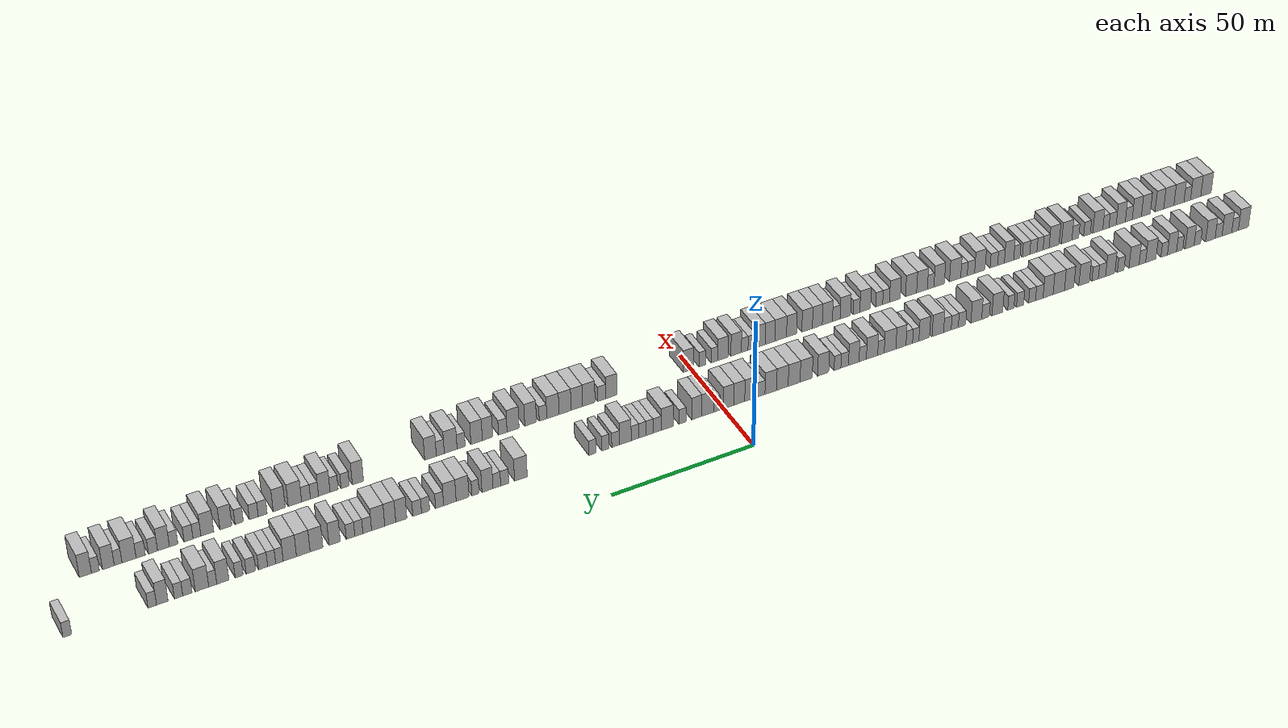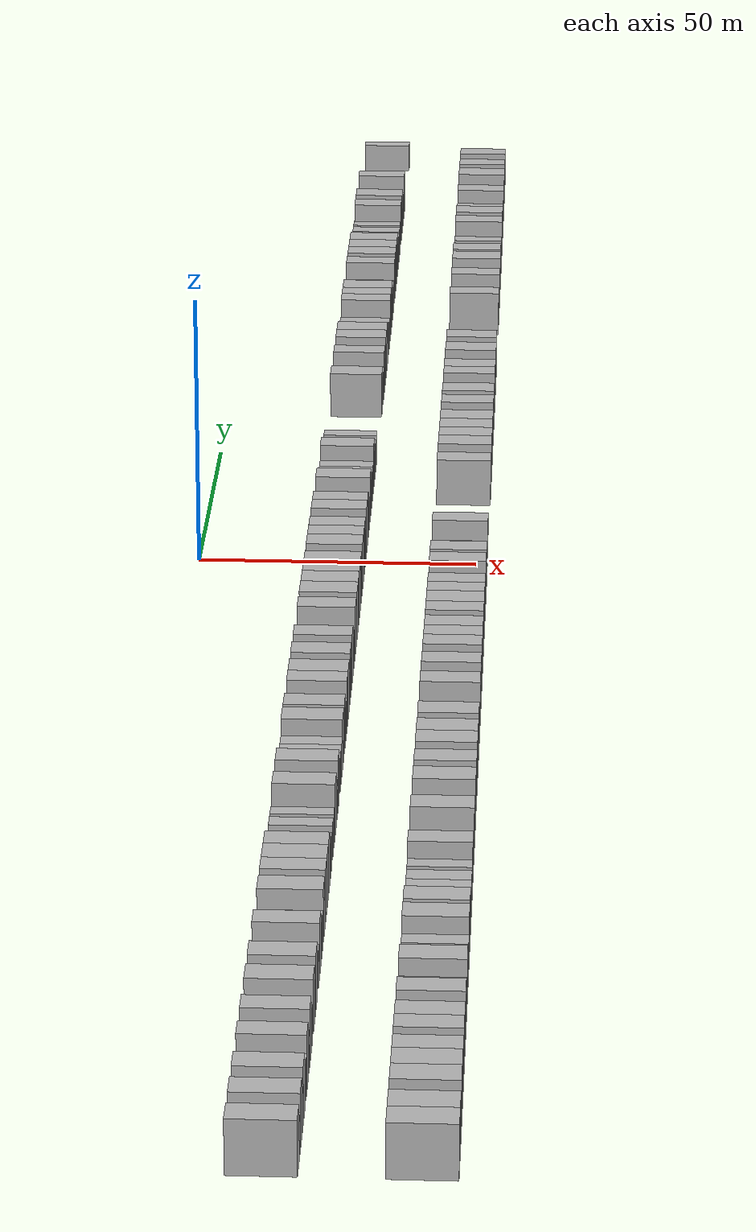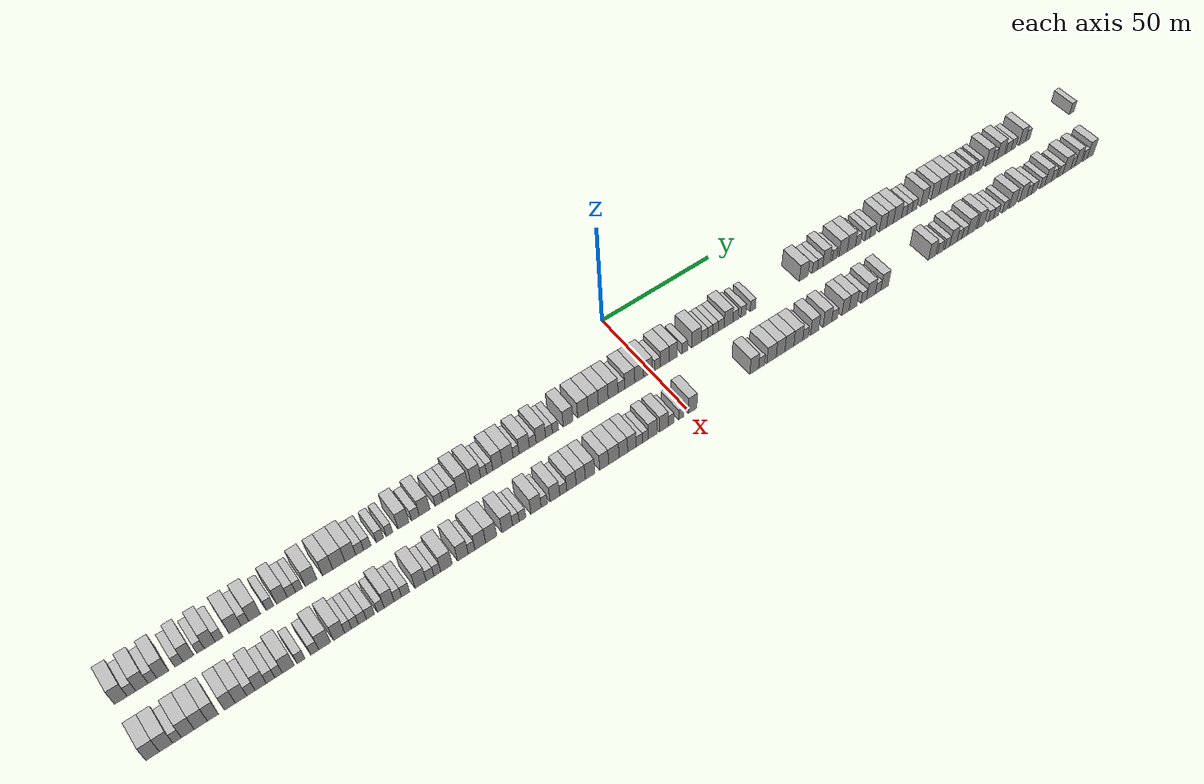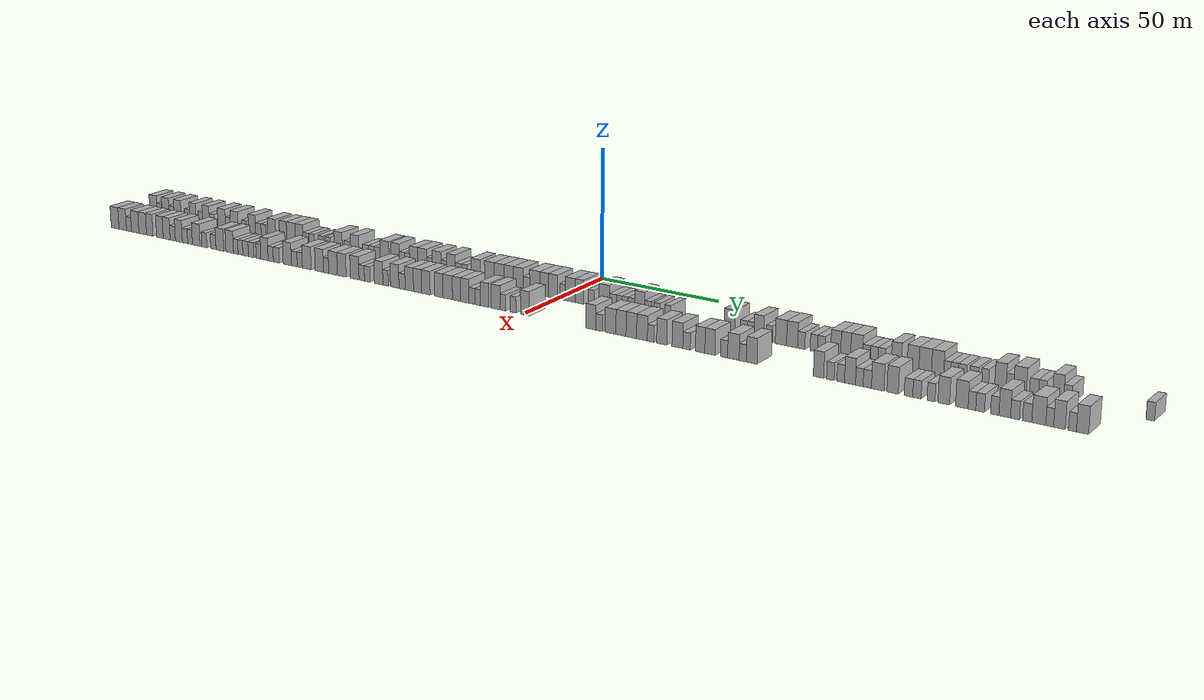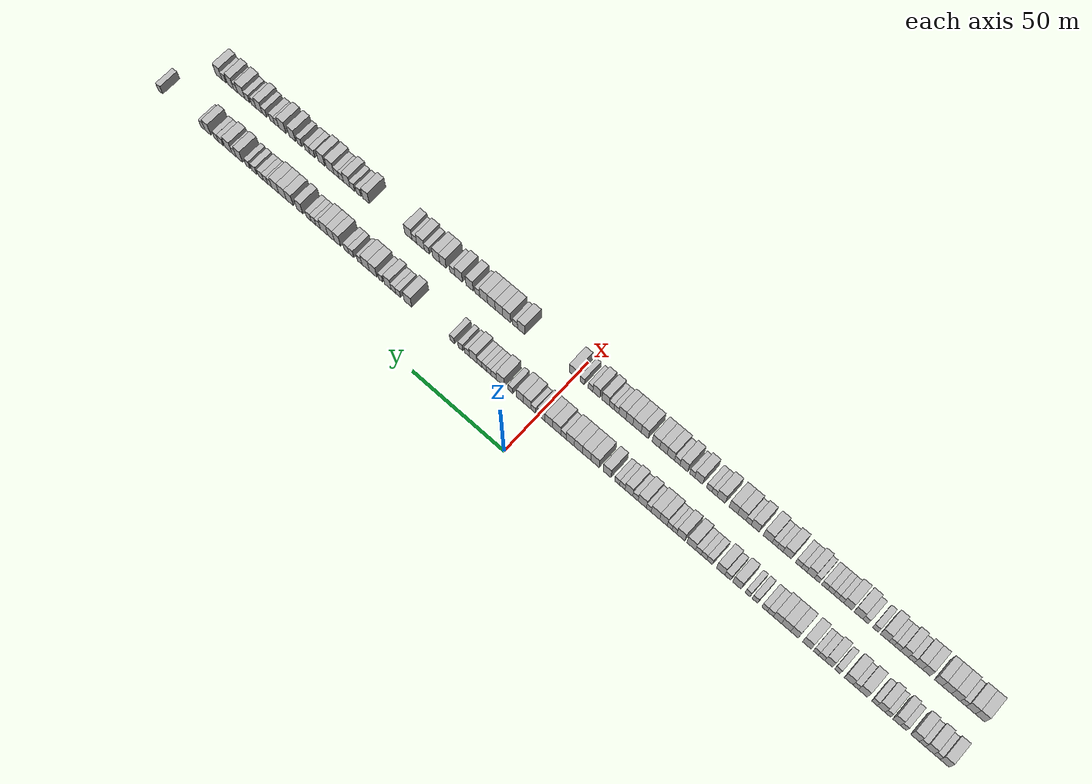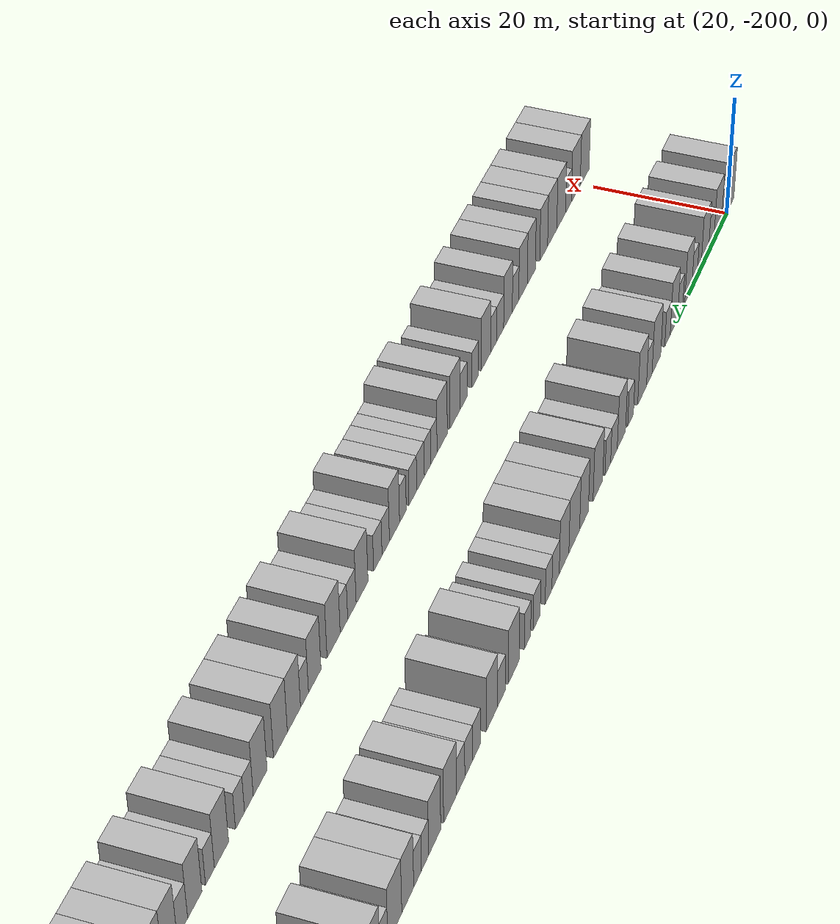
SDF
<sdf version="1.6">
 <world name="default">
  <scene>
   <sky><clouds><speed>12</speed></clouds></sky>
   <ambient>0.4 0.4 0.4 1</ambient>
   <background>0.7 0.7 0.7 1</background>
   <shadows>1</shadows>
  </scene>
  <gravity>0 0 -9.8066</gravity>
  <magnetic_field>6e-06 2.3e-05 -4.2e-05</magnetic_field>
  <physics default="0" name="default_physics" type="ode">
   <ode>
    <solver>
     <type>quick</type>
     <iters>10</iters>
     <sor>1.0</sor>
     <use_dynamic_moi_rescaling>0</use_dynamic_moi_rescaling>
    </solver>
    <constraints>
     <cfm>0</cfm>
     <erp>0.2</erp>
     <contact_max_correcting_vel>100</contact_max_correcting_vel>
     <contact_surface_layer>0.001</contact_surface_layer>
    </constraints>
   </ode>
   <max_step_size>0.004</max_step_size>
   <real_time_factor>1</real_time_factor>
   <real_time_update_rate>250</real_time_update_rate>
  </physics>
  <light name="sun" type="directional">
   <pose>0 0 10 0 0 0</pose>
   <diffuse>0.8 0.8 0.8 1</diffuse>
   <specular>0.2 0.2 0.2 1</specular>
   <attenuation>
    <range>1000</range>
    <constant>0.9</constant>
    <linear>0.01</linear>
    <quadratic>0.001</quadratic>
   </attenuation>
   <direction>-0.5 0.1 -0.9</direction>
  </light>
  <model name="building_1">
   <static>1</static>
   <pose>25.0000 -201.9250 0 0.000000 0.000000 0.000000</pose>
   <link name="link">
    <pose>0 0 4.50 0 0 0</pose>
    <collision name="collision"><geometry><box><size>10.0000 4.1501 9.0000</size></box></geometry></collision>
    <visual name="visual">
     <cast_shadows>0</cast_shadows>
     <geometry><box><size>10.0000 4.1501 9.0000</size></box></geometry>
     <material>
      <script>
       <uri>model://HANNAS_wall/materials/scripts</uri>
       <uri>model://HANNAS_wall/materials/textures</uri>
       <name>vrc/HANNAS_wall</name>
      </script>
     </material>
    </visual>
   </link>
  </model>
  <model name="building_2">
   <static>1</static>
   <pose>25.0000 -198.4543 0 0.000000 0.000000 0.000000</pose>
   <link name="link">
    <pose>0 0 3.00 0 0 0</pose>
    <collision name="collision"><geometry><box><size>10.0000 2.7912 6.0000</size></box></geometry></collision>
    <visual name="visual">
     <cast_shadows>0</cast_shadows>
     <geometry><box><size>10.0000 2.7912 6.0000</size></box></geometry>
     <material>
      <script>
       <uri>model://HANNAS_wall/materials/scripts</uri>
       <uri>model://HANNAS_wall/materials/textures</uri>
       <name>vrc/HANNAS_wall</name>
      </script>
     </material>
    </visual>
   </link>
  </model>
  <model name="building_3">
   <static>1</static>
   <pose>25.0000 -195.0415 0 0.000000 0.000000 0.000000</pose>
   <link name="link">
    <pose>0 0 4.50 0 0 0</pose>
    <collision name="collision"><geometry><box><size>10.0000 4.0345 9.0000</size></box></geometry></collision>
    <visual name="visual">
     <cast_shadows>0</cast_shadows>
     <geometry><box><size>10.0000 4.0345 9.0000</size></box></geometry>
     <material>
      <script>
       <uri>model://HANNAS_wall/materials/scripts</uri>
       <uri>model://HANNAS_wall/materials/textures</uri>
       <name>vrc/HANNAS_wall</name>
      </script>
     </material>
    </visual>
   </link>
  </model>
  <model name="building_4">
   <static>1</static>
   <pose>25.0000 -191.6100 0 0.000000 0.000000 0.000000</pose>
   <link name="link">
    <pose>0 0 3.00 0 0 0</pose>
    <collision name="collision"><geometry><box><size>10.0000 2.8284 6.0000</size></box></geometry></collision>
    <visual name="visual">
     <cast_shadows>0</cast_shadows>
     <geometry><box><size>10.0000 2.8284 6.0000</size></box></geometry>
     <material>
      <script>
       <uri>model://HANNAS_wall/materials/scripts</uri>
       <uri>model://HANNAS_wall/materials/textures</uri>
       <name>vrc/HANNAS_wall</name>
      </script>
     </material>
    </visual>
   </link>
  </model>
  <model name="building_5">
   <static>1</static>
   <pose>25.0000 -188.2119 0 0.000000 0.000000 0.000000</pose>
   <link name="link">
    <pose>0 0 4.50 0 0 0</pose>
    <collision name="collision"><geometry><box><size>10.0000 3.9679 9.0000</size></box></geometry></collision>
    <visual name="visual">
     <cast_shadows>0</cast_shadows>
     <geometry><box><size>10.0000 3.9679 9.0000</size></box></geometry>
     <material>
      <script>
       <uri>model://HANNAS_wall/materials/scripts</uri>
       <uri>model://HANNAS_wall/materials/textures</uri>
       <name>vrc/HANNAS_wall</name>
      </script>
     </material>
    </visual>
   </link>
  </model>
  <model name="building_6">
   <static>1</static>
   <pose>25.0000 -182.8537 0 0.000000 0.000000 0.000000</pose>
   <link name="link">
    <pose>0 0 3.00 0 0 0</pose>
    <collision name="collision"><geometry><box><size>10.0000 2.7484 6.0000</size></box></geometry></collision>
    <visual name="visual">
     <cast_shadows>0</cast_shadows>
     <geometry><box><size>10.0000 2.7484 6.0000</size></box></geometry>
     <material>
      <script>
       <uri>model://HANNAS_wall/materials/scripts</uri>
       <uri>model://HANNAS_wall/materials/textures</uri>
       <name>vrc/HANNAS_wall</name>
      </script>
     </material>
    </visual>
   </link>
  </model>
  <model name="building_7">
   <static>1</static>
   <pose>25.0000 -179.6666 0 0.000000 0.000000 0.000000</pose>
   <link name="link">
    <pose>0 0 4.50 0 0 0</pose>
    <collision name="collision"><geometry><box><size>10.0000 3.6259 9.0000</size></box></geometry></collision>
    <visual name="visual">
     <cast_shadows>0</cast_shadows>
     <geometry><box><size>10.0000 3.6259 9.0000</size></box></geometry>
     <material>
      <script>
       <uri>model://HANNAS_wall/materials/scripts</uri>
       <uri>model://HANNAS_wall/materials/textures</uri>
       <name>vrc/HANNAS_wall</name>
      </script>
     </material>
    </visual>
   </link>
  </model>
  <model name="building_8">
   <static>1</static>
   <pose>25.0000 -175.5762 0 0.000000 0.000000 0.000000</pose>
   <link name="link">
    <pose>0 0 3.00 0 0 0</pose>
    <collision name="collision"><geometry><box><size>10.0000 2.5548 6.0000</size></box></geometry></collision>
    <visual name="visual">
     <cast_shadows>0</cast_shadows>
     <geometry><box><size>10.0000 2.5548 6.0000</size></box></geometry>
     <material>
      <script>
       <uri>model://HANNAS_wall/materials/scripts</uri>
       <uri>model://HANNAS_wall/materials/textures</uri>
       <name>vrc/HANNAS_wall</name>
      </script>
     </material>
    </visual>
   </link>
  </model>
  <model name="building_9">
   <static>1</static>
   <pose>25.0000 -172.4359 0 0.000000 0.000000 0.000000</pose>
   <link name="link">
    <pose>0 0 4.50 0 0 0</pose>
    <collision name="collision"><geometry><box><size>10.0000 3.7259 9.0000</size></box></geometry></collision>
    <visual name="visual">
     <cast_shadows>0</cast_shadows>
     <geometry><box><size>10.0000 3.7259 9.0000</size></box></geometry>
     <material>
      <script>
       <uri>model://HANNAS_wall/materials/scripts</uri>
       <uri>model://HANNAS_wall/materials/textures</uri>
       <name>vrc/HANNAS_wall</name>
      </script>
     </material>
    </visual>
   </link>
  </model>
  <model name="building_10">
   <static>1</static>
   <pose>25.0000 -169.2458 0 0.000000 0.000000 0.000000</pose>
   <link name="link">
    <pose>0 0 3.00 0 0 0</pose>
    <collision name="collision"><geometry><box><size>10.0000 2.6541 6.0000</size></box></geometry></collision>
    <visual name="visual">
     <cast_shadows>0</cast_shadows>
     <geometry><box><size>10.0000 2.6541 6.0000</size></box></geometry>
     <material>
      <script>
       <uri>model://HANNAS_wall/materials/scripts</uri>
       <uri>model://HANNAS_wall/materials/textures</uri>
       <name>vrc/HANNAS_wall</name>
      </script>
     </material>
    </visual>
   </link>
  </model>
  <model name="building_11">
   <static>1</static>
   <pose>25.0000 -163.8209 0 0.000000 0.000000 0.000000</pose>
   <link name="link">
    <pose>0 0 4.50 0 0 0</pose>
    <collision name="collision"><geometry><box><size>10.0000 4.1957 9.0000</size></box></geometry></collision>
    <visual name="visual">
     <cast_shadows>0</cast_shadows>
     <geometry><box><size>10.0000 4.1957 9.0000</size></box></geometry>
     <material>
      <script>
       <uri>model://HANNAS_wall/materials/scripts</uri>
       <uri>model://HANNAS_wall/materials/textures</uri>
       <name>vrc/HANNAS_wall</name>
      </script>
     </material>
    </visual>
   </link>
  </model>
  <model name="building_12">
   <static>1</static>
   <pose>25.0000 -160.4024 0 0.000000 0.000000 0.000000</pose>
   <link name="link">
    <pose>0 0 3.00 0 0 0</pose>
    <collision name="collision"><geometry><box><size>10.0000 2.6414 6.0000</size></box></geometry></collision>
    <visual name="visual">
     <cast_shadows>0</cast_shadows>
     <geometry><box><size>10.0000 2.6414 6.0000</size></box></geometry>
     <material>
      <script>
       <uri>model://HANNAS_wall/materials/scripts</uri>
       <uri>model://HANNAS_wall/materials/textures</uri>
       <name>vrc/HANNAS_wall</name>
      </script>
     </material>
    </visual>
   </link>
  </model>
  <model name="building_13">
   <static>1</static>
   <pose>25.0000 -157.0162 0 0.000000 0.000000 0.000000</pose>
   <link name="link">
    <pose>0 0 4.50 0 0 0</pose>
    <collision name="collision"><geometry><box><size>10.0000 4.1309 9.0000</size></box></geometry></collision>
    <visual name="visual">
     <cast_shadows>0</cast_shadows>
     <geometry><box><size>10.0000 4.1309 9.0000</size></box></geometry>
     <material>
      <script>
       <uri>model://HANNAS_wall/materials/scripts</uri>
       <uri>model://HANNAS_wall/materials/textures</uri>
       <name>vrc/HANNAS_wall</name>
      </script>
     </material>
    </visual>
   </link>
  </model>
  <model name="building_14">
   <static>1</static>
   <pose>25.0000 -151.6285 0 0.000000 0.000000 0.000000</pose>
   <link name="link">
    <pose>0 0 3.00 0 0 0</pose>
    <collision name="collision"><geometry><box><size>10.0000 2.6447 6.0000</size></box></geometry></collision>
    <visual name="visual">
     <cast_shadows>0</cast_shadows>
     <geometry><box><size>10.0000 2.6447 6.0000</size></box></geometry>
     <material>
      <script>
       <uri>model://HANNAS_wall/materials/scripts</uri>
       <uri>model://HANNAS_wall/materials/textures</uri>
       <name>vrc/HANNAS_wall</name>
      </script>
     </material>
    </visual>
   </link>
  </model>
  <model name="building_15">
   <static>1</static>
   <pose>25.0000 -147.4297 0 0.000000 0.000000 0.000000</pose>
   <link name="link">
    <pose>0 0 4.50 0 0 0</pose>
    <collision name="collision"><geometry><box><size>10.0000 3.7528 9.0000</size></box></geometry></collision>
    <visual name="visual">
     <cast_shadows>0</cast_shadows>
     <geometry><box><size>10.0000 3.7528 9.0000</size></box></geometry>
     <material>
      <script>
       <uri>model://HANNAS_wall/materials/scripts</uri>
       <uri>model://HANNAS_wall/materials/textures</uri>
       <name>vrc/HANNAS_wall</name>
      </script>
     </material>
    </visual>
   </link>
  </model>
  <model name="building_16">
   <static>1</static>
   <pose>25.0000 -144.0700 0 0.000000 0.000000 0.000000</pose>
   <link name="link">
    <pose>0 0 3.00 0 0 0</pose>
    <collision name="collision"><geometry><box><size>10.0000 2.9665 6.0000</size></box></geometry></collision>
    <visual name="visual">
     <cast_shadows>0</cast_shadows>
     <geometry><box><size>10.0000 2.9665 6.0000</size></box></geometry>
     <material>
      <script>
       <uri>model://HANNAS_wall/materials/scripts</uri>
       <uri>model://HANNAS_wall/materials/textures</uri>
       <name>vrc/HANNAS_wall</name>
      </script>
     </material>
    </visual>
   </link>
  </model>
  <model name="building_17">
   <static>1</static>
   <pose>25.0000 -141.3345 0 0.000000 0.000000 0.000000</pose>
   <link name="link">
    <pose>0 0 3.00 0 0 0</pose>
    <collision name="collision"><geometry><box><size>10.0000 2.5046 6.0000</size></box></geometry></collision>
    <visual name="visual">
     <cast_shadows>0</cast_shadows>
     <geometry><box><size>10.0000 2.5046 6.0000</size></box></geometry>
     <material>
      <script>
       <uri>model://HANNAS_wall/materials/scripts</uri>
       <uri>model://HANNAS_wall/materials/textures</uri>
       <name>vrc/HANNAS_wall</name>
      </script>
     </material>
    </visual>
   </link>
  </model>
  <model name="building_18">
   <static>1</static>
   <pose>25.0000 -136.9713 0 0.000000 0.000000 0.000000</pose>
   <link name="link">
    <pose>0 0 4.50 0 0 0</pose>
    <collision name="collision"><geometry><box><size>10.0000 4.2218 9.0000</size></box></geometry></collision>
    <visual name="visual">
     <cast_shadows>0</cast_shadows>
     <geometry><box><size>10.0000 4.2218 9.0000</size></box></geometry>
     <material>
      <script>
       <uri>model://HANNAS_wall/materials/scripts</uri>
       <uri>model://HANNAS_wall/materials/textures</uri>
       <name>vrc/HANNAS_wall</name>
      </script>
     </material>
    </visual>
   </link>
  </model>
  <model name="building_19">
   <static>1</static>
   <pose>25.0000 -130.9918 0 0.000000 0.000000 0.000000</pose>
   <link name="link">
    <pose>0 0 4.50 0 0 0</pose>
    <collision name="collision"><geometry><box><size>10.0000 3.7371 9.0000</size></box></geometry></collision>
    <visual name="visual">
     <cast_shadows>0</cast_shadows>
     <geometry><box><size>10.0000 3.7371 9.0000</size></box></geometry>
     <material>
      <script>
       <uri>model://HANNAS_wall/materials/scripts</uri>
       <uri>model://HANNAS_wall/materials/textures</uri>
       <name>vrc/HANNAS_wall</name>
      </script>
     </material>
    </visual>
   </link>
  </model>
  <model name="building_20">
   <static>1</static>
   <pose>25.0000 -126.8824 0 0.000000 0.000000 0.000000</pose>
   <link name="link">
    <pose>0 0 4.50 0 0 0</pose>
    <collision name="collision"><geometry><box><size>10.0000 4.4817 9.0000</size></box></geometry></collision>
    <visual name="visual">
     <cast_shadows>0</cast_shadows>
     <geometry><box><size>10.0000 4.4817 9.0000</size></box></geometry>
     <material>
      <script>
       <uri>model://HANNAS_wall/materials/scripts</uri>
       <uri>model://HANNAS_wall/materials/textures</uri>
       <name>vrc/HANNAS_wall</name>
      </script>
     </material>
    </visual>
   </link>
  </model>
  <model name="building_21">
   <static>1</static>
   <pose>25.0000 -122.6475 0 0.000000 0.000000 0.000000</pose>
   <link name="link">
    <pose>0 0 4.50 0 0 0</pose>
    <collision name="collision"><geometry><box><size>10.0000 3.9882 9.0000</size></box></geometry></collision>
    <visual name="visual">
     <cast_shadows>0</cast_shadows>
     <geometry><box><size>10.0000 3.9882 9.0000</size></box></geometry>
     <material>
      <script>
       <uri>model://HANNAS_wall/materials/scripts</uri>
       <uri>model://HANNAS_wall/materials/textures</uri>
       <name>vrc/HANNAS_wall</name>
      </script>
     </material>
    </visual>
   </link>
  </model>
  <model name="building_22">
   <static>1</static>
   <pose>25.0000 -119.1737 0 0.000000 0.000000 0.000000</pose>
   <link name="link">
    <pose>0 0 3.00 0 0 0</pose>
    <collision name="collision"><geometry><box><size>10.0000 2.9594 6.0000</size></box></geometry></collision>
    <visual name="visual">
     <cast_shadows>0</cast_shadows>
     <geometry><box><size>10.0000 2.9594 6.0000</size></box></geometry>
     <material>
      <script>
       <uri>model://HANNAS_wall/materials/scripts</uri>
       <uri>model://HANNAS_wall/materials/textures</uri>
       <name>vrc/HANNAS_wall</name>
      </script>
     </material>
    </visual>
   </link>
  </model>
  <model name="building_23">
   <static>1</static>
   <pose>25.0000 -116.3464 0 0.000000 0.000000 0.000000</pose>
   <link name="link">
    <pose>0 0 3.00 0 0 0</pose>
    <collision name="collision"><geometry><box><size>10.0000 2.6951 6.0000</size></box></geometry></collision>
    <visual name="visual">
     <cast_shadows>0</cast_shadows>
     <geometry><box><size>10.0000 2.6951 6.0000</size></box></geometry>
     <material>
      <script>
       <uri>model://HANNAS_wall/materials/scripts</uri>
       <uri>model://HANNAS_wall/materials/textures</uri>
       <name>vrc/HANNAS_wall</name>
      </script>
     </material>
    </visual>
   </link>
  </model>
  <model name="building_24">
   <static>1</static>
   <pose>25.0000 -111.6198 0 0.000000 0.000000 0.000000</pose>
   <link name="link">
    <pose>0 0 3.00 0 0 0</pose>
    <collision name="collision"><geometry><box><size>10.0000 2.7581 6.0000</size></box></geometry></collision>
    <visual name="visual">
     <cast_shadows>0</cast_shadows>
     <geometry><box><size>10.0000 2.7581 6.0000</size></box></geometry>
     <material>
      <script>
       <uri>model://HANNAS_wall/materials/scripts</uri>
       <uri>model://HANNAS_wall/materials/textures</uri>
       <name>vrc/HANNAS_wall</name>
      </script>
     </material>
    </visual>
   </link>
  </model>
  <model name="building_25">
   <static>1</static>
   <pose>25.0000 -108.0218 0 0.000000 0.000000 0.000000</pose>
   <link name="link">
    <pose>0 0 3.00 0 0 0</pose>
    <collision name="collision"><geometry><box><size>10.0000 2.4379 6.0000</size></box></geometry></collision>
    <visual name="visual">
     <cast_shadows>0</cast_shadows>
     <geometry><box><size>10.0000 2.4379 6.0000</size></box></geometry>
     <material>
      <script>
       <uri>model://HANNAS_wall/materials/scripts</uri>
       <uri>model://HANNAS_wall/materials/textures</uri>
       <name>vrc/HANNAS_wall</name>
      </script>
     </material>
    </visual>
   </link>
  </model>
  <model name="building_26">
   <static>1</static>
   <pose>25.0000 -102.7193 0 0.000000 0.000000 0.000000</pose>
   <link name="link">
    <pose>0 0 4.50 0 0 0</pose>
    <collision name="collision"><geometry><box><size>10.0000 4.1671 9.0000</size></box></geometry></collision>
    <visual name="visual">
     <cast_shadows>0</cast_shadows>
     <geometry><box><size>10.0000 4.1671 9.0000</size></box></geometry>
     <material>
      <script>
       <uri>model://HANNAS_wall/materials/scripts</uri>
       <uri>model://HANNAS_wall/materials/textures</uri>
       <name>vrc/HANNAS_wall</name>
      </script>
     </material>
    </visual>
   </link>
  </model>
  <model name="building_27">
   <static>1</static>
   <pose>25.0000 -98.1461 0 0.000000 0.000000 0.000000</pose>
   <link name="link">
    <pose>0 0 3.00 0 0 0</pose>
    <collision name="collision"><geometry><box><size>10.0000 2.9792 6.0000</size></box></geometry></collision>
    <visual name="visual">
     <cast_shadows>0</cast_shadows>
     <geometry><box><size>10.0000 2.9792 6.0000</size></box></geometry>
     <material>
      <script>
       <uri>model://HANNAS_wall/materials/scripts</uri>
       <uri>model://HANNAS_wall/materials/textures</uri>
       <name>vrc/HANNAS_wall</name>
      </script>
     </material>
    </visual>
   </link>
  </model>
  <model name="building_28">
   <static>1</static>
   <pose>25.0000 -94.5732 0 0.000000 0.000000 0.000000</pose>
   <link name="link">
    <pose>0 0 4.50 0 0 0</pose>
    <collision name="collision"><geometry><box><size>10.0000 4.1664 9.0000</size></box></geometry></collision>
    <visual name="visual">
     <cast_shadows>0</cast_shadows>
     <geometry><box><size>10.0000 4.1664 9.0000</size></box></geometry>
     <material>
      <script>
       <uri>model://HANNAS_wall/materials/scripts</uri>
       <uri>model://HANNAS_wall/materials/textures</uri>
       <name>vrc/HANNAS_wall</name>
      </script>
     </material>
    </visual>
   </link>
  </model>
  <model name="building_29">
   <static>1</static>
   <pose>25.0000 -89.0513 0 0.000000 0.000000 0.000000</pose>
   <link name="link">
    <pose>0 0 3.00 0 0 0</pose>
    <collision name="collision"><geometry><box><size>10.0000 2.8774 6.0000</size></box></geometry></collision>
    <visual name="visual">
     <cast_shadows>0</cast_shadows>
     <geometry><box><size>10.0000 2.8774 6.0000</size></box></geometry>
     <material>
      <script>
       <uri>model://HANNAS_wall/materials/scripts</uri>
       <uri>model://HANNAS_wall/materials/textures</uri>
       <name>vrc/HANNAS_wall</name>
      </script>
     </material>
    </visual>
   </link>
  </model>
  <model name="building_30">
   <static>1</static>
   <pose>25.0000 -86.2458 0 0.000000 0.000000 0.000000</pose>
   <link name="link">
    <pose>0 0 3.00 0 0 0</pose>
    <collision name="collision"><geometry><box><size>10.0000 2.7337 6.0000</size></box></geometry></collision>
    <visual name="visual">
     <cast_shadows>0</cast_shadows>
     <geometry><box><size>10.0000 2.7337 6.0000</size></box></geometry>
     <material>
      <script>
       <uri>model://HANNAS_wall/materials/scripts</uri>
       <uri>model://HANNAS_wall/materials/textures</uri>
       <name>vrc/HANNAS_wall</name>
      </script>
     </material>
    </visual>
   </link>
  </model>
  <model name="building_31">
   <static>1</static>
   <pose>25.0000 -83.4233 0 0.000000 0.000000 0.000000</pose>
   <link name="link">
    <pose>0 0 3.00 0 0 0</pose>
    <collision name="collision"><geometry><box><size>10.0000 2.9113 6.0000</size></box></geometry></collision>
    <visual name="visual">
     <cast_shadows>0</cast_shadows>
     <geometry><box><size>10.0000 2.9113 6.0000</size></box></geometry>
     <material>
      <script>
       <uri>model://HANNAS_wall/materials/scripts</uri>
       <uri>model://HANNAS_wall/materials/textures</uri>
       <name>vrc/HANNAS_wall</name>
      </script>
     </material>
    </visual>
   </link>
  </model>
  <model name="building_32">
   <static>1</static>
   <pose>25.0000 -79.7604 0 0.000000 0.000000 0.000000</pose>
   <link name="link">
    <pose>0 0 4.50 0 0 0</pose>
    <collision name="collision"><geometry><box><size>10.0000 4.4144 9.0000</size></box></geometry></collision>
    <visual name="visual">
     <cast_shadows>0</cast_shadows>
     <geometry><box><size>10.0000 4.4144 9.0000</size></box></geometry>
     <material>
      <script>
       <uri>model://HANNAS_wall/materials/scripts</uri>
       <uri>model://HANNAS_wall/materials/textures</uri>
       <name>vrc/HANNAS_wall</name>
      </script>
     </material>
    </visual>
   </link>
  </model>
  <model name="building_33">
   <static>1</static>
   <pose>25.0000 -74.5264 0 0.000000 0.000000 0.000000</pose>
   <link name="link">
    <pose>0 0 4.50 0 0 0</pose>
    <collision name="collision"><geometry><box><size>10.0000 4.0536 9.0000</size></box></geometry></collision>
    <visual name="visual">
     <cast_shadows>0</cast_shadows>
     <geometry><box><size>10.0000 4.0536 9.0000</size></box></geometry>
     <material>
      <script>
       <uri>model://HANNAS_wall/materials/scripts</uri>
       <uri>model://HANNAS_wall/materials/textures</uri>
       <name>vrc/HANNAS_wall</name>
      </script>
     </material>
    </visual>
   </link>
  </model>
  <model name="building_34">
   <static>1</static>
   <pose>25.0000 -71.2966 0 0.000000 0.000000 0.000000</pose>
   <link name="link">
    <pose>0 0 3.00 0 0 0</pose>
    <collision name="collision"><geometry><box><size>10.0000 2.4060 6.0000</size></box></geometry></collision>
    <visual name="visual">
     <cast_shadows>0</cast_shadows>
     <geometry><box><size>10.0000 2.4060 6.0000</size></box></geometry>
     <material>
      <script>
       <uri>model://HANNAS_wall/materials/scripts</uri>
       <uri>model://HANNAS_wall/materials/textures</uri>
       <name>vrc/HANNAS_wall</name>
      </script>
     </material>
    </visual>
   </link>
  </model>
  <model name="building_35">
   <static>1</static>
   <pose>25.0000 -68.8379 0 0.000000 0.000000 0.000000</pose>
   <link name="link">
    <pose>0 0 3.00 0 0 0</pose>
    <collision name="collision"><geometry><box><size>10.0000 2.5114 6.0000</size></box></geometry></collision>
    <visual name="visual">
     <cast_shadows>0</cast_shadows>
     <geometry><box><size>10.0000 2.5114 6.0000</size></box></geometry>
     <material>
      <script>
       <uri>model://HANNAS_wall/materials/scripts</uri>
       <uri>model://HANNAS_wall/materials/textures</uri>
       <name>vrc/HANNAS_wall</name>
      </script>
     </material>
    </visual>
   </link>
  </model>
  <model name="building_36">
   <static>1</static>
   <pose>25.0000 -65.6650 0 0.000000 0.000000 0.000000</pose>
   <link name="link">
    <pose>0 0 4.50 0 0 0</pose>
    <collision name="collision"><geometry><box><size>10.0000 3.8343 9.0000</size></box></geometry></collision>
    <visual name="visual">
     <cast_shadows>0</cast_shadows>
     <geometry><box><size>10.0000 3.8343 9.0000</size></box></geometry>
     <material>
      <script>
       <uri>model://HANNAS_wall/materials/scripts</uri>
       <uri>model://HANNAS_wall/materials/textures</uri>
       <name>vrc/HANNAS_wall</name>
      </script>
     </material>
    </visual>
   </link>
  </model>
  <model name="building_37">
   <static>1</static>
   <pose>25.0000 -61.5360 0 0.000000 0.000000 0.000000</pose>
   <link name="link">
    <pose>0 0 4.50 0 0 0</pose>
    <collision name="collision"><geometry><box><size>10.0000 4.4238 9.0000</size></box></geometry></collision>
    <visual name="visual">
     <cast_shadows>0</cast_shadows>
     <geometry><box><size>10.0000 4.4238 9.0000</size></box></geometry>
     <material>
      <script>
       <uri>model://HANNAS_wall/materials/scripts</uri>
       <uri>model://HANNAS_wall/materials/textures</uri>
       <name>vrc/HANNAS_wall</name>
      </script>
     </material>
    </visual>
   </link>
  </model>
  <model name="building_38">
   <static>1</static>
   <pose>25.0000 -58.1043 0 0.000000 0.000000 0.000000</pose>
   <link name="link">
    <pose>0 0 3.00 0 0 0</pose>
    <collision name="collision"><geometry><box><size>10.0000 2.4395 6.0000</size></box></geometry></collision>
    <visual name="visual">
     <cast_shadows>0</cast_shadows>
     <geometry><box><size>10.0000 2.4395 6.0000</size></box></geometry>
     <material>
      <script>
       <uri>model://HANNAS_wall/materials/scripts</uri>
       <uri>model://HANNAS_wall/materials/textures</uri>
       <name>vrc/HANNAS_wall</name>
      </script>
     </material>
    </visual>
   </link>
  </model>
  <model name="building_39">
   <static>1</static>
   <pose>25.0000 -54.7499 0 0.000000 0.000000 0.000000</pose>
   <link name="link">
    <pose>0 0 4.50 0 0 0</pose>
    <collision name="collision"><geometry><box><size>10.0000 4.2694 9.0000</size></box></geometry></collision>
    <visual name="visual">
     <cast_shadows>0</cast_shadows>
     <geometry><box><size>10.0000 4.2694 9.0000</size></box></geometry>
     <material>
      <script>
       <uri>model://HANNAS_wall/materials/scripts</uri>
       <uri>model://HANNAS_wall/materials/textures</uri>
       <name>vrc/HANNAS_wall</name>
      </script>
     </material>
    </visual>
   </link>
  </model>
  <model name="building_40">
   <static>1</static>
   <pose>25.0000 -51.2329 0 0.000000 0.000000 0.000000</pose>
   <link name="link">
    <pose>0 0 3.00 0 0 0</pose>
    <collision name="collision"><geometry><box><size>10.0000 2.7645 6.0000</size></box></geometry></collision>
    <visual name="visual">
     <cast_shadows>0</cast_shadows>
     <geometry><box><size>10.0000 2.7645 6.0000</size></box></geometry>
     <material>
      <script>
       <uri>model://HANNAS_wall/materials/scripts</uri>
       <uri>model://HANNAS_wall/materials/textures</uri>
       <name>vrc/HANNAS_wall</name>
      </script>
     </material>
    </visual>
   </link>
  </model>
  <model name="building_41">
   <static>1</static>
   <pose>25.0000 -47.8789 0 0.000000 0.000000 0.000000</pose>
   <link name="link">
    <pose>0 0 4.50 0 0 0</pose>
    <collision name="collision"><geometry><box><size>10.0000 3.9436 9.0000</size></box></geometry></collision>
    <visual name="visual">
     <cast_shadows>0</cast_shadows>
     <geometry><box><size>10.0000 3.9436 9.0000</size></box></geometry>
     <material>
      <script>
       <uri>model://HANNAS_wall/materials/scripts</uri>
       <uri>model://HANNAS_wall/materials/textures</uri>
       <name>vrc/HANNAS_wall</name>
      </script>
     </material>
    </visual>
   </link>
  </model>
  <model name="building_42">
   <static>1</static>
   <pose>25.0000 -44.4795 0 0.000000 0.000000 0.000000</pose>
   <link name="link">
    <pose>0 0 3.00 0 0 0</pose>
    <collision name="collision"><geometry><box><size>10.0000 2.8552 6.0000</size></box></geometry></collision>
    <visual name="visual">
     <cast_shadows>0</cast_shadows>
     <geometry><box><size>10.0000 2.8552 6.0000</size></box></geometry>
     <material>
      <script>
       <uri>model://HANNAS_wall/materials/scripts</uri>
       <uri>model://HANNAS_wall/materials/textures</uri>
       <name>vrc/HANNAS_wall</name>
      </script>
     </material>
    </visual>
   </link>
  </model>
  <model name="building_43">
   <static>1</static>
   <pose>25.0000 -41.7935 0 0.000000 0.000000 0.000000</pose>
   <link name="link">
    <pose>0 0 3.00 0 0 0</pose>
    <collision name="collision"><geometry><box><size>10.0000 2.5168 6.0000</size></box></geometry></collision>
    <visual name="visual">
     <cast_shadows>0</cast_shadows>
     <geometry><box><size>10.0000 2.5168 6.0000</size></box></geometry>
     <material>
      <script>
       <uri>model://HANNAS_wall/materials/scripts</uri>
       <uri>model://HANNAS_wall/materials/textures</uri>
       <name>vrc/HANNAS_wall</name>
      </script>
     </material>
    </visual>
   </link>
  </model>
  <model name="building_44">
   <static>1</static>
   <pose>25.0000 -36.4770 0 0.000000 0.000000 0.000000</pose>
   <link name="link">
    <pose>0 0 4.50 0 0 0</pose>
    <collision name="collision"><geometry><box><size>10.0000 4.1163 9.0000</size></box></geometry></collision>
    <visual name="visual">
     <cast_shadows>0</cast_shadows>
     <geometry><box><size>10.0000 4.1163 9.0000</size></box></geometry>
     <material>
      <script>
       <uri>model://HANNAS_wall/materials/scripts</uri>
       <uri>model://HANNAS_wall/materials/textures</uri>
       <name>vrc/HANNAS_wall</name>
      </script>
     </material>
    </visual>
   </link>
  </model>
  <model name="building_45">
   <static>1</static>
   <pose>25.0000 -30.1749 0 0.000000 0.000000 0.000000</pose>
   <link name="link">
    <pose>0 0 4.50 0 0 0</pose>
    <collision name="collision"><geometry><box><size>10.0000 4.4879 9.0000</size></box></geometry></collision>
    <visual name="visual">
     <cast_shadows>0</cast_shadows>
     <geometry><box><size>10.0000 4.4879 9.0000</size></box></geometry>
     <material>
      <script>
       <uri>model://HANNAS_wall/materials/scripts</uri>
       <uri>model://HANNAS_wall/materials/textures</uri>
       <name>vrc/HANNAS_wall</name>
      </script>
     </material>
    </visual>
   </link>
  </model>
  <model name="building_46">
   <static>1</static>
   <pose>25.0000 -25.7231 0 0.000000 0.000000 0.000000</pose>
   <link name="link">
    <pose>0 0 4.50 0 0 0</pose>
    <collision name="collision"><geometry><box><size>10.0000 4.4156 9.0000</size></box></geometry></collision>
    <visual name="visual">
     <cast_shadows>0</cast_shadows>
     <geometry><box><size>10.0000 4.4156 9.0000</size></box></geometry>
     <material>
      <script>
       <uri>model://HANNAS_wall/materials/scripts</uri>
       <uri>model://HANNAS_wall/materials/textures</uri>
       <name>vrc/HANNAS_wall</name>
      </script>
     </material>
    </visual>
   </link>
  </model>
  <model name="building_47">
   <static>1</static>
   <pose>25.0000 -21.4024 0 0.000000 0.000000 0.000000</pose>
   <link name="link">
    <pose>0 0 4.50 0 0 0</pose>
    <collision name="collision"><geometry><box><size>10.0000 4.2259 9.0000</size></box></geometry></collision>
    <visual name="visual">
     <cast_shadows>0</cast_shadows>
     <geometry><box><size>10.0000 4.2259 9.0000</size></box></geometry>
     <material>
      <script>
       <uri>model://HANNAS_wall/materials/scripts</uri>
       <uri>model://HANNAS_wall/materials/textures</uri>
       <name>vrc/HANNAS_wall</name>
      </script>
     </material>
    </visual>
   </link>
  </model>
  <model name="building_48">
   <static>1</static>
   <pose>25.0000 -17.1323 0 0.000000 0.000000 0.000000</pose>
   <link name="link">
    <pose>0 0 4.50 0 0 0</pose>
    <collision name="collision"><geometry><box><size>10.0000 4.3141 9.0000</size></box></geometry></collision>
    <visual name="visual">
     <cast_shadows>0</cast_shadows>
     <geometry><box><size>10.0000 4.3141 9.0000</size></box></geometry>
     <material>
      <script>
       <uri>model://HANNAS_wall/materials/scripts</uri>
       <uri>model://HANNAS_wall/materials/textures</uri>
       <name>vrc/HANNAS_wall</name>
      </script>
     </material>
    </visual>
   </link>
  </model>
  <model name="building_49">
   <static>1</static>
   <pose>25.0000 -13.5283 0 0.000000 0.000000 0.000000</pose>
   <link name="link">
    <pose>0 0 3.00 0 0 0</pose>
    <collision name="collision"><geometry><box><size>10.0000 2.8940 6.0000</size></box></geometry></collision>
    <visual name="visual">
     <cast_shadows>0</cast_shadows>
     <geometry><box><size>10.0000 2.8940 6.0000</size></box></geometry>
     <material>
      <script>
       <uri>model://HANNAS_wall/materials/scripts</uri>
       <uri>model://HANNAS_wall/materials/textures</uri>
       <name>vrc/HANNAS_wall</name>
      </script>
     </material>
    </visual>
   </link>
  </model>
  <model name="building_50">
   <static>1</static>
   <pose>25.0000 -9.8389 0 0.000000 0.000000 0.000000</pose>
   <link name="link">
    <pose>0 0 4.50 0 0 0</pose>
    <collision name="collision"><geometry><box><size>10.0000 4.4849 9.0000</size></box></geometry></collision>
    <visual name="visual">
     <cast_shadows>0</cast_shadows>
     <geometry><box><size>10.0000 4.4849 9.0000</size></box></geometry>
     <material>
      <script>
       <uri>model://HANNAS_wall/materials/scripts</uri>
       <uri>model://HANNAS_wall/materials/textures</uri>
       <name>vrc/HANNAS_wall</name>
      </script>
     </material>
    </visual>
   </link>
  </model>
  <model name="building_51">
   <static>1</static>
   <pose>25.0000 -5.6319 0 0.000000 0.000000 0.000000</pose>
   <link name="link">
    <pose>0 0 4.50 0 0 0</pose>
    <collision name="collision"><geometry><box><size>10.0000 3.9292 9.0000</size></box></geometry></collision>
    <visual name="visual">
     <cast_shadows>0</cast_shadows>
     <geometry><box><size>10.0000 3.9292 9.0000</size></box></geometry>
     <material>
      <script>
       <uri>model://HANNAS_wall/materials/scripts</uri>
       <uri>model://HANNAS_wall/materials/textures</uri>
       <name>vrc/HANNAS_wall</name>
      </script>
     </material>
    </visual>
   </link>
  </model>
  <model name="building_52">
   <static>1</static>
   <pose>25.0000 -1.7157 0 0.000000 0.000000 0.000000</pose>
   <link name="link">
    <pose>0 0 4.50 0 0 0</pose>
    <collision name="collision"><geometry><box><size>10.0000 3.9032 9.0000</size></box></geometry></collision>
    <visual name="visual">
     <cast_shadows>0</cast_shadows>
     <geometry><box><size>10.0000 3.9032 9.0000</size></box></geometry>
     <material>
      <script>
       <uri>model://HANNAS_wall/materials/scripts</uri>
       <uri>model://HANNAS_wall/materials/textures</uri>
       <name>vrc/HANNAS_wall</name>
      </script>
     </material>
    </visual>
   </link>
  </model>
  <model name="building_53">
   <static>1</static>
   <pose>25.0000 2.4711 0 0.000000 0.000000 0.000000</pose>
   <link name="link">
    <pose>0 0 3.00 0 0 0</pose>
    <collision name="collision"><geometry><box><size>10.0000 2.4704 6.0000</size></box></geometry></collision>
    <visual name="visual">
     <cast_shadows>0</cast_shadows>
     <geometry><box><size>10.0000 2.4704 6.0000</size></box></geometry>
     <material>
      <script>
       <uri>model://HANNAS_wall/materials/scripts</uri>
       <uri>model://HANNAS_wall/materials/textures</uri>
       <name>vrc/HANNAS_wall</name>
      </script>
     </material>
    </visual>
   </link>
  </model>
  <model name="building_54">
   <static>1</static>
   <pose>25.0000 5.7965 0 0.000000 0.000000 0.000000</pose>
   <link name="link">
    <pose>0 0 4.50 0 0 0</pose>
    <collision name="collision"><geometry><box><size>10.0000 4.1805 9.0000</size></box></geometry></collision>
    <visual name="visual">
     <cast_shadows>0</cast_shadows>
     <geometry><box><size>10.0000 4.1805 9.0000</size></box></geometry>
     <material>
      <script>
       <uri>model://HANNAS_wall/materials/scripts</uri>
       <uri>model://HANNAS_wall/materials/textures</uri>
       <name>vrc/HANNAS_wall</name>
      </script>
     </material>
    </visual>
   </link>
  </model>
  <model name="building_55">
   <static>1</static>
   <pose>25.0000 9.7286 0 0.000000 0.000000 0.000000</pose>
   <link name="link">
    <pose>0 0 4.50 0 0 0</pose>
    <collision name="collision"><geometry><box><size>10.0000 3.6836 9.0000</size></box></geometry></collision>
    <visual name="visual">
     <cast_shadows>0</cast_shadows>
     <geometry><box><size>10.0000 3.6836 9.0000</size></box></geometry>
     <material>
      <script>
       <uri>model://HANNAS_wall/materials/scripts</uri>
       <uri>model://HANNAS_wall/materials/textures</uri>
       <name>vrc/HANNAS_wall</name>
      </script>
     </material>
    </visual>
   </link>
  </model>
  <model name="building_56">
   <static>1</static>
   <pose>25.0000 14.8592 0 0.000000 0.000000 0.000000</pose>
   <link name="link">
    <pose>0 0 3.00 0 0 0</pose>
    <collision name="collision"><geometry><box><size>10.0000 2.5777 6.0000</size></box></geometry></collision>
    <visual name="visual">
     <cast_shadows>0</cast_shadows>
     <geometry><box><size>10.0000 2.5777 6.0000</size></box></geometry>
     <material>
      <script>
       <uri>model://HANNAS_wall/materials/scripts</uri>
       <uri>model://HANNAS_wall/materials/textures</uri>
       <name>vrc/HANNAS_wall</name>
      </script>
     </material>
    </visual>
   </link>
  </model>
  <model name="building_57">
   <static>1</static>
   <pose>25.0000 20.3237 0 0.000000 0.000000 0.000000</pose>
   <link name="link">
    <pose>0 0 4.50 0 0 0</pose>
    <collision name="collision"><geometry><box><size>10.0000 4.3511 9.0000</size></box></geometry></collision>
    <visual name="visual">
     <cast_shadows>0</cast_shadows>
     <geometry><box><size>10.0000 4.3511 9.0000</size></box></geometry>
     <material>
      <script>
       <uri>model://HANNAS_wall/materials/scripts</uri>
       <uri>model://HANNAS_wall/materials/textures</uri>
       <name>vrc/HANNAS_wall</name>
      </script>
     </material>
    </visual>
   </link>
  </model>
  <model name="building_58">
   <static>1</static>
   <pose>25.0000 23.9629 0 0.000000 0.000000 0.000000</pose>
   <link name="link">
    <pose>0 0 3.00 0 0 0</pose>
    <collision name="collision"><geometry><box><size>10.0000 2.9274 6.0000</size></box></geometry></collision>
    <visual name="visual">
     <cast_shadows>0</cast_shadows>
     <geometry><box><size>10.0000 2.9274 6.0000</size></box></geometry>
     <material>
      <script>
       <uri>model://HANNAS_wall/materials/scripts</uri>
       <uri>model://HANNAS_wall/materials/textures</uri>
       <name>vrc/HANNAS_wall</name>
      </script>
     </material>
    </visual>
   </link>
  </model>
  <model name="building_59">
   <static>1</static>
   <pose>25.0000 26.6528 0 0.000000 0.000000 0.000000</pose>
   <link name="link">
    <pose>0 0 3.00 0 0 0</pose>
    <collision name="collision"><geometry><box><size>10.0000 2.4523 6.0000</size></box></geometry></collision>
    <visual name="visual">
     <cast_shadows>0</cast_shadows>
     <geometry><box><size>10.0000 2.4523 6.0000</size></box></geometry>
     <material>
      <script>
       <uri>model://HANNAS_wall/materials/scripts</uri>
       <uri>model://HANNAS_wall/materials/textures</uri>
       <name>vrc/HANNAS_wall</name>
      </script>
     </material>
    </visual>
   </link>
  </model>
  <model name="building_60">
   <static>1</static>
   <pose>25.0000 29.1491 0 0.000000 0.000000 0.000000</pose>
   <link name="link">
    <pose>0 0 3.00 0 0 0</pose>
    <collision name="collision"><geometry><box><size>10.0000 2.5403 6.0000</size></box></geometry></collision>
    <visual name="visual">
     <cast_shadows>0</cast_shadows>
     <geometry><box><size>10.0000 2.5403 6.0000</size></box></geometry>
     <material>
      <script>
       <uri>model://HANNAS_wall/materials/scripts</uri>
       <uri>model://HANNAS_wall/materials/textures</uri>
       <name>vrc/HANNAS_wall</name>
      </script>
     </material>
    </visual>
   </link>
  </model>
  <model name="building_61">
   <static>1</static>
   <pose>25.0000 31.7835 0 0.000000 0.000000 0.000000</pose>
   <link name="link">
    <pose>0 0 3.00 0 0 0</pose>
    <collision name="collision"><geometry><box><size>10.0000 2.7285 6.0000</size></box></geometry></collision>
    <visual name="visual">
     <cast_shadows>0</cast_shadows>
     <geometry><box><size>10.0000 2.7285 6.0000</size></box></geometry>
     <material>
      <script>
       <uri>model://HANNAS_wall/materials/scripts</uri>
       <uri>model://HANNAS_wall/materials/textures</uri>
       <name>vrc/HANNAS_wall</name>
      </script>
     </material>
    </visual>
   </link>
  </model>
  <model name="building_62">
   <static>1</static>
   <pose>25.0000 35.2118 0 0.000000 0.000000 0.000000</pose>
   <link name="link">
    <pose>0 0 4.50 0 0 0</pose>
    <collision name="collision"><geometry><box><size>10.0000 4.1281 9.0000</size></box></geometry></collision>
    <visual name="visual">
     <cast_shadows>0</cast_shadows>
     <geometry><box><size>10.0000 4.1281 9.0000</size></box></geometry>
     <material>
      <script>
       <uri>model://HANNAS_wall/materials/scripts</uri>
       <uri>model://HANNAS_wall/materials/textures</uri>
       <name>vrc/HANNAS_wall</name>
      </script>
     </material>
    </visual>
   </link>
  </model>
  <model name="building_63">
   <static>1</static>
   <pose>25.0000 38.6452 0 0.000000 0.000000 0.000000</pose>
   <link name="link">
    <pose>0 0 3.00 0 0 0</pose>
    <collision name="collision"><geometry><box><size>10.0000 2.7387 6.0000</size></box></geometry></collision>
    <visual name="visual">
     <cast_shadows>0</cast_shadows>
     <geometry><box><size>10.0000 2.7387 6.0000</size></box></geometry>
     <material>
      <script>
       <uri>model://HANNAS_wall/materials/scripts</uri>
       <uri>model://HANNAS_wall/materials/textures</uri>
       <name>vrc/HANNAS_wall</name>
      </script>
     </material>
    </visual>
   </link>
  </model>
  <model name="building_64">
   <static>1</static>
   <pose>25.0000 42.2577 0 0.000000 0.000000 0.000000</pose>
   <link name="link">
    <pose>0 0 3.00 0 0 0</pose>
    <collision name="collision"><geometry><box><size>10.0000 2.4863 6.0000</size></box></geometry></collision>
    <visual name="visual">
     <cast_shadows>0</cast_shadows>
     <geometry><box><size>10.0000 2.4863 6.0000</size></box></geometry>
     <material>
      <script>
       <uri>model://HANNAS_wall/materials/scripts</uri>
       <uri>model://HANNAS_wall/materials/textures</uri>
       <name>vrc/HANNAS_wall</name>
      </script>
     </material>
    </visual>
   </link>
  </model>
  <model name="building_65">
   <static>1</static>
   <pose>25.0000 46.8011 0 0.000000 0.000000 0.000000</pose>
   <link name="link">
    <pose>0 0 3.00 0 0 0</pose>
    <collision name="collision"><geometry><box><size>10.0000 2.6005 6.0000</size></box></geometry></collision>
    <visual name="visual">
     <cast_shadows>0</cast_shadows>
     <geometry><box><size>10.0000 2.6005 6.0000</size></box></geometry>
     <material>
      <script>
       <uri>model://HANNAS_wall/materials/scripts</uri>
       <uri>model://HANNAS_wall/materials/textures</uri>
       <name>vrc/HANNAS_wall</name>
      </script>
     </material>
    </visual>
   </link>
  </model>
  <model name="building_66">
   <static>1</static>
   <pose>25.0000 71.6259 0 0.000000 0.000000 0.000000</pose>
   <link name="link">
    <pose>0 0 4.50 0 0 0</pose>
    <collision name="collision"><geometry><box><size>10.0000 4.3496 9.0000</size></box></geometry></collision>
    <visual name="visual">
     <cast_shadows>0</cast_shadows>
     <geometry><box><size>10.0000 4.3496 9.0000</size></box></geometry>
     <material>
      <script>
       <uri>model://HANNAS_wall/materials/scripts</uri>
       <uri>model://HANNAS_wall/materials/textures</uri>
       <name>vrc/HANNAS_wall</name>
      </script>
     </material>
    </visual>
   </link>
  </model>
  <model name="building_67">
   <static>1</static>
   <pose>25.0000 77.1780 0 0.000000 0.000000 0.000000</pose>
   <link name="link">
    <pose>0 0 3.00 0 0 0</pose>
    <collision name="collision"><geometry><box><size>10.0000 2.7546 6.0000</size></box></geometry></collision>
    <visual name="visual">
     <cast_shadows>0</cast_shadows>
     <geometry><box><size>10.0000 2.7546 6.0000</size></box></geometry>
     <material>
      <script>
       <uri>model://HANNAS_wall/materials/scripts</uri>
       <uri>model://HANNAS_wall/materials/textures</uri>
       <name>vrc/HANNAS_wall</name>
      </script>
     </material>
    </visual>
   </link>
  </model>
  <model name="building_68">
   <static>1</static>
   <pose>25.0000 79.8654 0 0.000000 0.000000 0.000000</pose>
   <link name="link">
    <pose>0 0 3.00 0 0 0</pose>
    <collision name="collision"><geometry><box><size>10.0000 2.6202 6.0000</size></box></geometry></collision>
    <visual name="visual">
     <cast_shadows>0</cast_shadows>
     <geometry><box><size>10.0000 2.6202 6.0000</size></box></geometry>
     <material>
      <script>
       <uri>model://HANNAS_wall/materials/scripts</uri>
       <uri>model://HANNAS_wall/materials/textures</uri>
       <name>vrc/HANNAS_wall</name>
      </script>
     </material>
    </visual>
   </link>
  </model>
  <model name="building_69">
   <static>1</static>
   <pose>25.0000 83.0649 0 0.000000 0.000000 0.000000</pose>
   <link name="link">
    <pose>0 0 4.50 0 0 0</pose>
    <collision name="collision"><geometry><box><size>10.0000 3.7788 9.0000</size></box></geometry></collision>
    <visual name="visual">
     <cast_shadows>0</cast_shadows>
     <geometry><box><size>10.0000 3.7788 9.0000</size></box></geometry>
     <material>
      <script>
       <uri>model://HANNAS_wall/materials/scripts</uri>
       <uri>model://HANNAS_wall/materials/textures</uri>
       <name>vrc/HANNAS_wall</name>
      </script>
     </material>
    </visual>
   </link>
  </model>
  <model name="building_70">
   <static>1</static>
   <pose>25.0000 87.1570 0 0.000000 0.000000 0.000000</pose>
   <link name="link">
    <pose>0 0 3.00 0 0 0</pose>
    <collision name="collision"><geometry><box><size>10.0000 2.4053 6.0000</size></box></geometry></collision>
    <visual name="visual">
     <cast_shadows>0</cast_shadows>
     <geometry><box><size>10.0000 2.4053 6.0000</size></box></geometry>
     <material>
      <script>
       <uri>model://HANNAS_wall/materials/scripts</uri>
       <uri>model://HANNAS_wall/materials/textures</uri>
       <name>vrc/HANNAS_wall</name>
      </script>
     </material>
    </visual>
   </link>
  </model>
  <model name="building_71">
   <static>1</static>
   <pose>25.0000 91.5323 0 0.000000 0.000000 0.000000</pose>
   <link name="link">
    <pose>0 0 4.50 0 0 0</pose>
    <collision name="collision"><geometry><box><size>10.0000 4.3453 9.0000</size></box></geometry></collision>
    <visual name="visual">
     <cast_shadows>0</cast_shadows>
     <geometry><box><size>10.0000 4.3453 9.0000</size></box></geometry>
     <material>
      <script>
       <uri>model://HANNAS_wall/materials/scripts</uri>
       <uri>model://HANNAS_wall/materials/textures</uri>
       <name>vrc/HANNAS_wall</name>
      </script>
     </material>
    </visual>
   </link>
  </model>
  <model name="building_72">
   <static>1</static>
   <pose>25.0000 95.8232 0 0.000000 0.000000 0.000000</pose>
   <link name="link">
    <pose>0 0 4.50 0 0 0</pose>
    <collision name="collision"><geometry><box><size>10.0000 4.2366 9.0000</size></box></geometry></collision>
    <visual name="visual">
     <cast_shadows>0</cast_shadows>
     <geometry><box><size>10.0000 4.2366 9.0000</size></box></geometry>
     <material>
      <script>
       <uri>model://HANNAS_wall/materials/scripts</uri>
       <uri>model://HANNAS_wall/materials/textures</uri>
       <name>vrc/HANNAS_wall</name>
      </script>
     </material>
    </visual>
   </link>
  </model>
  <model name="building_73">
   <static>1</static>
   <pose>25.0000 99.2963 0 0.000000 0.000000 0.000000</pose>
   <link name="link">
    <pose>0 0 3.00 0 0 0</pose>
    <collision name="collision"><geometry><box><size>10.0000 2.7095 6.0000</size></box></geometry></collision>
    <visual name="visual">
     <cast_shadows>0</cast_shadows>
     <geometry><box><size>10.0000 2.7095 6.0000</size></box></geometry>
     <material>
      <script>
       <uri>model://HANNAS_wall/materials/scripts</uri>
       <uri>model://HANNAS_wall/materials/textures</uri>
       <name>vrc/HANNAS_wall</name>
      </script>
     </material>
    </visual>
   </link>
  </model>
  <model name="building_74">
   <static>1</static>
   <pose>25.0000 104.0020 0 0.000000 0.000000 0.000000</pose>
   <link name="link">
    <pose>0 0 3.00 0 0 0</pose>
    <collision name="collision"><geometry><box><size>10.0000 2.7020 6.0000</size></box></geometry></collision>
    <visual name="visual">
     <cast_shadows>0</cast_shadows>
     <geometry><box><size>10.0000 2.7020 6.0000</size></box></geometry>
     <material>
      <script>
       <uri>model://HANNAS_wall/materials/scripts</uri>
       <uri>model://HANNAS_wall/materials/textures</uri>
       <name>vrc/HANNAS_wall</name>
      </script>
     </material>
    </visual>
   </link>
  </model>
  <model name="building_75">
   <static>1</static>
   <pose>25.0000 106.8193 0 0.000000 0.000000 0.000000</pose>
   <link name="link">
    <pose>0 0 3.00 0 0 0</pose>
    <collision name="collision"><geometry><box><size>10.0000 2.9324 6.0000</size></box></geometry></collision>
    <visual name="visual">
     <cast_shadows>0</cast_shadows>
     <geometry><box><size>10.0000 2.9324 6.0000</size></box></geometry>
     <material>
      <script>
       <uri>model://HANNAS_wall/materials/scripts</uri>
       <uri>model://HANNAS_wall/materials/textures</uri>
       <name>vrc/HANNAS_wall</name>
      </script>
     </material>
    </visual>
   </link>
  </model>
  <model name="building_76">
   <static>1</static>
   <pose>25.0000 112.1365 0 0.000000 0.000000 0.000000</pose>
   <link name="link">
    <pose>0 0 4.50 0 0 0</pose>
    <collision name="collision"><geometry><box><size>10.0000 3.7021 9.0000</size></box></geometry></collision>
    <visual name="visual">
     <cast_shadows>0</cast_shadows>
     <geometry><box><size>10.0000 3.7021 9.0000</size></box></geometry>
     <material>
      <script>
       <uri>model://HANNAS_wall/materials/scripts</uri>
       <uri>model://HANNAS_wall/materials/textures</uri>
       <name>vrc/HANNAS_wall</name>
      </script>
     </material>
    </visual>
   </link>
  </model>
  <model name="building_77">
   <static>1</static>
   <pose>25.0000 115.8191 0 0.000000 0.000000 0.000000</pose>
   <link name="link">
    <pose>0 0 4.50 0 0 0</pose>
    <collision name="collision"><geometry><box><size>10.0000 3.6630 9.0000</size></box></geometry></collision>
    <visual name="visual">
     <cast_shadows>0</cast_shadows>
     <geometry><box><size>10.0000 3.6630 9.0000</size></box></geometry>
     <material>
      <script>
       <uri>model://HANNAS_wall/materials/scripts</uri>
       <uri>model://HANNAS_wall/materials/textures</uri>
       <name>vrc/HANNAS_wall</name>
      </script>
     </material>
    </visual>
   </link>
  </model>
  <model name="building_78">
   <static>1</static>
   <pose>25.0000 119.8326 0 0.000000 0.000000 0.000000</pose>
   <link name="link">
    <pose>0 0 4.50 0 0 0</pose>
    <collision name="collision"><geometry><box><size>10.0000 4.3639 9.0000</size></box></geometry></collision>
    <visual name="visual">
     <cast_shadows>0</cast_shadows>
     <geometry><box><size>10.0000 4.3639 9.0000</size></box></geometry>
     <material>
      <script>
       <uri>model://HANNAS_wall/materials/scripts</uri>
       <uri>model://HANNAS_wall/materials/textures</uri>
       <name>vrc/HANNAS_wall</name>
      </script>
     </material>
    </visual>
   </link>
  </model>
  <model name="building_79">
   <static>1</static>
   <pose>25.0000 123.4523 0 0.000000 0.000000 0.000000</pose>
   <link name="link">
    <pose>0 0 3.00 0 0 0</pose>
    <collision name="collision"><geometry><box><size>10.0000 2.8755 6.0000</size></box></geometry></collision>
    <visual name="visual">
     <cast_shadows>0</cast_shadows>
     <geometry><box><size>10.0000 2.8755 6.0000</size></box></geometry>
     <material>
      <script>
       <uri>model://HANNAS_wall/materials/scripts</uri>
       <uri>model://HANNAS_wall/materials/textures</uri>
       <name>vrc/HANNAS_wall</name>
      </script>
     </material>
    </visual>
   </link>
  </model>
  <model name="building_80">
   <static>1</static>
   <pose>25.0000 126.2203 0 0.000000 0.000000 0.000000</pose>
   <link name="link">
    <pose>0 0 3.00 0 0 0</pose>
    <collision name="collision"><geometry><box><size>10.0000 2.6606 6.0000</size></box></geometry></collision>
    <visual name="visual">
     <cast_shadows>0</cast_shadows>
     <geometry><box><size>10.0000 2.6606 6.0000</size></box></geometry>
     <material>
      <script>
       <uri>model://HANNAS_wall/materials/scripts</uri>
       <uri>model://HANNAS_wall/materials/textures</uri>
       <name>vrc/HANNAS_wall</name>
      </script>
     </material>
    </visual>
   </link>
  </model>
  <model name="building_81">
   <static>1</static>
   <pose>25.0000 128.9449 0 0.000000 0.000000 0.000000</pose>
   <link name="link">
    <pose>0 0 3.00 0 0 0</pose>
    <collision name="collision"><geometry><box><size>10.0000 2.7885 6.0000</size></box></geometry></collision>
    <visual name="visual">
     <cast_shadows>0</cast_shadows>
     <geometry><box><size>10.0000 2.7885 6.0000</size></box></geometry>
     <material>
      <script>
       <uri>model://HANNAS_wall/materials/scripts</uri>
       <uri>model://HANNAS_wall/materials/textures</uri>
       <name>vrc/HANNAS_wall</name>
      </script>
     </material>
    </visual>
   </link>
  </model>
  <model name="building_82">
   <static>1</static>
   <pose>25.0000 134.1834 0 0.000000 0.000000 0.000000</pose>
   <link name="link">
    <pose>0 0 4.50 0 0 0</pose>
    <collision name="collision"><geometry><box><size>10.0000 3.6885 9.0000</size></box></geometry></collision>
    <visual name="visual">
     <cast_shadows>0</cast_shadows>
     <geometry><box><size>10.0000 3.6885 9.0000</size></box></geometry>
     <material>
      <script>
       <uri>model://HANNAS_wall/materials/scripts</uri>
       <uri>model://HANNAS_wall/materials/textures</uri>
       <name>vrc/HANNAS_wall</name>
      </script>
     </material>
    </visual>
   </link>
  </model>
  <model name="building_83">
   <static>1</static>
   <pose>25.0000 140.1214 0 0.000000 0.000000 0.000000</pose>
   <link name="link">
    <pose>0 0 4.50 0 0 0</pose>
    <collision name="collision"><geometry><box><size>10.0000 4.1876 9.0000</size></box></geometry></collision>
    <visual name="visual">
     <cast_shadows>0</cast_shadows>
     <geometry><box><size>10.0000 4.1876 9.0000</size></box></geometry>
     <material>
      <script>
       <uri>model://HANNAS_wall/materials/scripts</uri>
       <uri>model://HANNAS_wall/materials/textures</uri>
       <name>vrc/HANNAS_wall</name>
      </script>
     </material>
    </visual>
   </link>
  </model>
  <model name="building_84">
   <static>1</static>
   <pose>25.0000 144.4341 0 0.000000 0.000000 0.000000</pose>
   <link name="link">
    <pose>0 0 4.50 0 0 0</pose>
    <collision name="collision"><geometry><box><size>10.0000 4.4377 9.0000</size></box></geometry></collision>
    <visual name="visual">
     <cast_shadows>0</cast_shadows>
     <geometry><box><size>10.0000 4.4377 9.0000</size></box></geometry>
     <material>
      <script>
       <uri>model://HANNAS_wall/materials/scripts</uri>
       <uri>model://HANNAS_wall/materials/textures</uri>
       <name>vrc/HANNAS_wall</name>
      </script>
     </material>
    </visual>
   </link>
  </model>
  <model name="building_85">
   <static>1</static>
   <pose>25.0000 148.8020 0 0.000000 0.000000 0.000000</pose>
   <link name="link">
    <pose>0 0 4.50 0 0 0</pose>
    <collision name="collision"><geometry><box><size>10.0000 4.2981 9.0000</size></box></geometry></collision>
    <visual name="visual">
     <cast_shadows>0</cast_shadows>
     <geometry><box><size>10.0000 4.2981 9.0000</size></box></geometry>
     <material>
      <script>
       <uri>model://HANNAS_wall/materials/scripts</uri>
       <uri>model://HANNAS_wall/materials/textures</uri>
       <name>vrc/HANNAS_wall</name>
      </script>
     </material>
    </visual>
   </link>
  </model>
  <model name="building_86">
   <static>1</static>
   <pose>25.0000 152.1677 0 0.000000 0.000000 0.000000</pose>
   <link name="link">
    <pose>0 0 3.00 0 0 0</pose>
    <collision name="collision"><geometry><box><size>10.0000 2.4332 6.0000</size></box></geometry></collision>
    <visual name="visual">
     <cast_shadows>0</cast_shadows>
     <geometry><box><size>10.0000 2.4332 6.0000</size></box></geometry>
     <material>
      <script>
       <uri>model://HANNAS_wall/materials/scripts</uri>
       <uri>model://HANNAS_wall/materials/textures</uri>
       <name>vrc/HANNAS_wall</name>
      </script>
     </material>
    </visual>
   </link>
  </model>
  <model name="building_87">
   <static>1</static>
   <pose>25.0000 154.6846 0 0.000000 0.000000 0.000000</pose>
   <link name="link">
    <pose>0 0 3.00 0 0 0</pose>
    <collision name="collision"><geometry><box><size>10.0000 2.6007 6.0000</size></box></geometry></collision>
    <visual name="visual">
     <cast_shadows>0</cast_shadows>
     <geometry><box><size>10.0000 2.6007 6.0000</size></box></geometry>
     <material>
      <script>
       <uri>model://HANNAS_wall/materials/scripts</uri>
       <uri>model://HANNAS_wall/materials/textures</uri>
       <name>vrc/HANNAS_wall</name>
      </script>
     </material>
    </visual>
   </link>
  </model>
  <model name="building_88">
   <static>1</static>
   <pose>25.0000 157.4364 0 0.000000 0.000000 0.000000</pose>
   <link name="link">
    <pose>0 0 3.00 0 0 0</pose>
    <collision name="collision"><geometry><box><size>10.0000 2.9029 6.0000</size></box></geometry></collision>
    <visual name="visual">
     <cast_shadows>0</cast_shadows>
     <geometry><box><size>10.0000 2.9029 6.0000</size></box></geometry>
     <material>
      <script>
       <uri>model://HANNAS_wall/materials/scripts</uri>
       <uri>model://HANNAS_wall/materials/textures</uri>
       <name>vrc/HANNAS_wall</name>
      </script>
     </material>
    </visual>
   </link>
  </model>
  <model name="building_89">
   <static>1</static>
   <pose>25.0000 161.3820 0 0.000000 0.000000 0.000000</pose>
   <link name="link">
    <pose>0 0 3.00 0 0 0</pose>
    <collision name="collision"><geometry><box><size>10.0000 2.9883 6.0000</size></box></geometry></collision>
    <visual name="visual">
     <cast_shadows>0</cast_shadows>
     <geometry><box><size>10.0000 2.9883 6.0000</size></box></geometry>
     <material>
      <script>
       <uri>model://HANNAS_wall/materials/scripts</uri>
       <uri>model://HANNAS_wall/materials/textures</uri>
       <name>vrc/HANNAS_wall</name>
      </script>
     </material>
    </visual>
   </link>
  </model>
  <model name="building_90">
   <static>1</static>
   <pose>25.0000 165.1503 0 0.000000 0.000000 0.000000</pose>
   <link name="link">
    <pose>0 0 3.00 0 0 0</pose>
    <collision name="collision"><geometry><box><size>10.0000 2.5482 6.0000</size></box></geometry></collision>
    <visual name="visual">
     <cast_shadows>0</cast_shadows>
     <geometry><box><size>10.0000 2.5482 6.0000</size></box></geometry>
     <material>
      <script>
       <uri>model://HANNAS_wall/materials/scripts</uri>
       <uri>model://HANNAS_wall/materials/textures</uri>
       <name>vrc/HANNAS_wall</name>
      </script>
     </material>
    </visual>
   </link>
  </model>
  <model name="building_91">
   <static>1</static>
   <pose>25.0000 170.3662 0 0.000000 0.000000 0.000000</pose>
   <link name="link">
    <pose>0 0 4.50 0 0 0</pose>
    <collision name="collision"><geometry><box><size>10.0000 3.8836 9.0000</size></box></geometry></collision>
    <visual name="visual">
     <cast_shadows>0</cast_shadows>
     <geometry><box><size>10.0000 3.8836 9.0000</size></box></geometry>
     <material>
      <script>
       <uri>model://HANNAS_wall/materials/scripts</uri>
       <uri>model://HANNAS_wall/materials/textures</uri>
       <name>vrc/HANNAS_wall</name>
      </script>
     </material>
    </visual>
   </link>
  </model>
  <model name="building_92">
   <static>1</static>
   <pose>25.0000 173.5777 0 0.000000 0.000000 0.000000</pose>
   <link name="link">
    <pose>0 0 3.00 0 0 0</pose>
    <collision name="collision"><geometry><box><size>10.0000 2.5394 6.0000</size></box></geometry></collision>
    <visual name="visual">
     <cast_shadows>0</cast_shadows>
     <geometry><box><size>10.0000 2.5394 6.0000</size></box></geometry>
     <material>
      <script>
       <uri>model://HANNAS_wall/materials/scripts</uri>
       <uri>model://HANNAS_wall/materials/textures</uri>
       <name>vrc/HANNAS_wall</name>
      </script>
     </material>
    </visual>
   </link>
  </model>
  <model name="building_93">
   <static>1</static>
   <pose>25.0000 176.9889 0 0.000000 0.000000 0.000000</pose>
   <link name="link">
    <pose>0 0 4.50 0 0 0</pose>
    <collision name="collision"><geometry><box><size>10.0000 4.2830 9.0000</size></box></geometry></collision>
    <visual name="visual">
     <cast_shadows>0</cast_shadows>
     <geometry><box><size>10.0000 4.2830 9.0000</size></box></geometry>
     <material>
      <script>
       <uri>model://HANNAS_wall/materials/scripts</uri>
       <uri>model://HANNAS_wall/materials/textures</uri>
       <name>vrc/HANNAS_wall</name>
      </script>
     </material>
    </visual>
   </link>
  </model>
  <model name="building_94">
   <static>1</static>
   <pose>25.0000 181.6113 0 0.000000 0.000000 0.000000</pose>
   <link name="link">
    <pose>0 0 3.00 0 0 0</pose>
    <collision name="collision"><geometry><box><size>10.0000 2.9618 6.0000</size></box></geometry></collision>
    <visual name="visual">
     <cast_shadows>0</cast_shadows>
     <geometry><box><size>10.0000 2.9618 6.0000</size></box></geometry>
     <material>
      <script>
       <uri>model://HANNAS_wall/materials/scripts</uri>
       <uri>model://HANNAS_wall/materials/textures</uri>
       <name>vrc/HANNAS_wall</name>
      </script>
     </material>
    </visual>
   </link>
  </model>
  <model name="building_95">
   <static>1</static>
   <pose>25.0000 184.4083 0 0.000000 0.000000 0.000000</pose>
   <link name="link">
    <pose>0 0 3.00 0 0 0</pose>
    <collision name="collision"><geometry><box><size>10.0000 2.6321 6.0000</size></box></geometry></collision>
    <visual name="visual">
     <cast_shadows>0</cast_shadows>
     <geometry><box><size>10.0000 2.6321 6.0000</size></box></geometry>
     <material>
      <script>
       <uri>model://HANNAS_wall/materials/scripts</uri>
       <uri>model://HANNAS_wall/materials/textures</uri>
       <name>vrc/HANNAS_wall</name>
      </script>
     </material>
    </visual>
   </link>
  </model>
  <model name="building_96">
   <static>1</static>
   <pose>25.0000 189.5480 0 0.000000 0.000000 0.000000</pose>
   <link name="link">
    <pose>0 0 4.50 0 0 0</pose>
    <collision name="collision"><geometry><box><size>10.0000 3.6474 9.0000</size></box></geometry></collision>
    <visual name="visual">
     <cast_shadows>0</cast_shadows>
     <geometry><box><size>10.0000 3.6474 9.0000</size></box></geometry>
     <material>
      <script>
       <uri>model://HANNAS_wall/materials/scripts</uri>
       <uri>model://HANNAS_wall/materials/textures</uri>
       <name>vrc/HANNAS_wall</name>
      </script>
     </material>
    </visual>
   </link>
  </model>
  <model name="building_97">
   <static>1</static>
   <pose>25.0000 192.7031 0 0.000000 0.000000 0.000000</pose>
   <link name="link">
    <pose>0 0 3.00 0 0 0</pose>
    <collision name="collision"><geometry><box><size>10.0000 2.6629 6.0000</size></box></geometry></collision>
    <visual name="visual">
     <cast_shadows>0</cast_shadows>
     <geometry><box><size>10.0000 2.6629 6.0000</size></box></geometry>
     <material>
      <script>
       <uri>model://HANNAS_wall/materials/scripts</uri>
       <uri>model://HANNAS_wall/materials/textures</uri>
       <name>vrc/HANNAS_wall</name>
      </script>
     </material>
    </visual>
   </link>
  </model>
  <model name="building_98">
   <static>1</static>
   <pose>25.0000 219.0721 0 0.000000 0.000000 0.000000</pose>
   <link name="link">
    <pose>0 0 3.00 0 0 0</pose>
    <collision name="collision"><geometry><box><size>10.0000 2.6917 6.0000</size></box></geometry></collision>
    <visual name="visual">
     <cast_shadows>0</cast_shadows>
     <geometry><box><size>10.0000 2.6917 6.0000</size></box></geometry>
     <material>
      <script>
       <uri>model://HANNAS_wall/materials/scripts</uri>
       <uri>model://HANNAS_wall/materials/textures</uri>
       <name>vrc/HANNAS_wall</name>
      </script>
     </material>
    </visual>
   </link>
  </model>
  <model name="building_99">
   <static>1</static>
   <pose>47.0000 -201.8210 0 0.000000 0.000000 0.000000</pose>
   <link name="link">
    <pose>0 0 4.50 0 0 0</pose>
    <collision name="collision"><geometry><box><size>10.0000 4.3580 9.0000</size></box></geometry></collision>
    <visual name="visual">
     <cast_shadows>0</cast_shadows>
     <geometry><box><size>10.0000 4.3580 9.0000</size></box></geometry>
     <material>
      <script>
       <uri>model://HANNAS_wall/materials/scripts</uri>
       <uri>model://HANNAS_wall/materials/textures</uri>
       <name>vrc/HANNAS_wall</name>
      </script>
     </material>
    </visual>
   </link>
  </model>
  <model name="building_100">
   <static>1</static>
   <pose>47.0000 -197.4983 0 0.000000 0.000000 0.000000</pose>
   <link name="link">
    <pose>0 0 4.50 0 0 0</pose>
    <collision name="collision"><geometry><box><size>10.0000 4.2874 9.0000</size></box></geometry></collision>
    <visual name="visual">
     <cast_shadows>0</cast_shadows>
     <geometry><box><size>10.0000 4.2874 9.0000</size></box></geometry>
     <material>
      <script>
       <uri>model://HANNAS_wall/materials/scripts</uri>
       <uri>model://HANNAS_wall/materials/textures</uri>
       <name>vrc/HANNAS_wall</name>
      </script>
     </material>
    </visual>
   </link>
  </model>
  <model name="building_101">
   <static>1</static>
   <pose>47.0000 -193.9791 0 0.000000 0.000000 0.000000</pose>
   <link name="link">
    <pose>0 0 3.00 0 0 0</pose>
    <collision name="collision"><geometry><box><size>10.0000 2.7510 6.0000</size></box></geometry></collision>
    <visual name="visual">
     <cast_shadows>0</cast_shadows>
     <geometry><box><size>10.0000 2.7510 6.0000</size></box></geometry>
     <material>
      <script>
       <uri>model://HANNAS_wall/materials/scripts</uri>
       <uri>model://HANNAS_wall/materials/textures</uri>
       <name>vrc/HANNAS_wall</name>
      </script>
     </material>
    </visual>
   </link>
  </model>
  <model name="building_102">
   <static>1</static>
   <pose>47.0000 -190.5100 0 0.000000 0.000000 0.000000</pose>
   <link name="link">
    <pose>0 0 4.50 0 0 0</pose>
    <collision name="collision"><geometry><box><size>10.0000 4.1871 9.0000</size></box></geometry></collision>
    <visual name="visual">
     <cast_shadows>0</cast_shadows>
     <geometry><box><size>10.0000 4.1871 9.0000</size></box></geometry>
     <material>
      <script>
       <uri>model://HANNAS_wall/materials/scripts</uri>
       <uri>model://HANNAS_wall/materials/textures</uri>
       <name>vrc/HANNAS_wall</name>
      </script>
     </material>
    </visual>
   </link>
  </model>
  <model name="building_103">
   <static>1</static>
   <pose>47.0000 -186.2833 0 0.000000 0.000000 0.000000</pose>
   <link name="link">
    <pose>0 0 4.50 0 0 0</pose>
    <collision name="collision"><geometry><box><size>10.0000 4.2664 9.0000</size></box></geometry></collision>
    <visual name="visual">
     <cast_shadows>0</cast_shadows>
     <geometry><box><size>10.0000 4.2664 9.0000</size></box></geometry>
     <material>
      <script>
       <uri>model://HANNAS_wall/materials/scripts</uri>
       <uri>model://HANNAS_wall/materials/textures</uri>
       <name>vrc/HANNAS_wall</name>
      </script>
     </material>
    </visual>
   </link>
  </model>
  <model name="building_104">
   <static>1</static>
   <pose>47.0000 -182.3498 0 0.000000 0.000000 0.000000</pose>
   <link name="link">
    <pose>0 0 4.50 0 0 0</pose>
    <collision name="collision"><geometry><box><size>10.0000 3.6005 9.0000</size></box></geometry></collision>
    <visual name="visual">
     <cast_shadows>0</cast_shadows>
     <geometry><box><size>10.0000 3.6005 9.0000</size></box></geometry>
     <material>
      <script>
       <uri>model://HANNAS_wall/materials/scripts</uri>
       <uri>model://HANNAS_wall/materials/textures</uri>
       <name>vrc/HANNAS_wall</name>
      </script>
     </material>
    </visual>
   </link>
  </model>
  <model name="building_105">
   <static>1</static>
   <pose>47.0000 -176.7281 0 0.000000 0.000000 0.000000</pose>
   <link name="link">
    <pose>0 0 4.50 0 0 0</pose>
    <collision name="collision"><geometry><box><size>10.0000 3.6428 9.0000</size></box></geometry></collision>
    <visual name="visual">
     <cast_shadows>0</cast_shadows>
     <geometry><box><size>10.0000 3.6428 9.0000</size></box></geometry>
     <material>
      <script>
       <uri>model://HANNAS_wall/materials/scripts</uri>
       <uri>model://HANNAS_wall/materials/textures</uri>
       <name>vrc/HANNAS_wall</name>
      </script>
     </material>
    </visual>
   </link>
  </model>
  <model name="building_106">
   <static>1</static>
   <pose>47.0000 -173.0132 0 0.000000 0.000000 0.000000</pose>
   <link name="link">
    <pose>0 0 4.50 0 0 0</pose>
    <collision name="collision"><geometry><box><size>10.0000 3.7869 9.0000</size></box></geometry></collision>
    <visual name="visual">
     <cast_shadows>0</cast_shadows>
     <geometry><box><size>10.0000 3.7869 9.0000</size></box></geometry>
     <material>
      <script>
       <uri>model://HANNAS_wall/materials/scripts</uri>
       <uri>model://HANNAS_wall/materials/textures</uri>
       <name>vrc/HANNAS_wall</name>
      </script>
     </material>
    </visual>
   </link>
  </model>
  <model name="building_107">
   <static>1</static>
   <pose>47.0000 -169.7011 0 0.000000 0.000000 0.000000</pose>
   <link name="link">
    <pose>0 0 3.00 0 0 0</pose>
    <collision name="collision"><geometry><box><size>10.0000 2.8374 6.0000</size></box></geometry></collision>
    <visual name="visual">
     <cast_shadows>0</cast_shadows>
     <geometry><box><size>10.0000 2.8374 6.0000</size></box></geometry>
     <material>
      <script>
       <uri>model://HANNAS_wall/materials/scripts</uri>
       <uri>model://HANNAS_wall/materials/textures</uri>
       <name>vrc/HANNAS_wall</name>
      </script>
     </material>
    </visual>
   </link>
  </model>
  <model name="building_108">
   <static>1</static>
   <pose>47.0000 -166.4025 0 0.000000 0.000000 0.000000</pose>
   <link name="link">
    <pose>0 0 4.50 0 0 0</pose>
    <collision name="collision"><geometry><box><size>10.0000 3.7596 9.0000</size></box></geometry></collision>
    <visual name="visual">
     <cast_shadows>0</cast_shadows>
     <geometry><box><size>10.0000 3.7596 9.0000</size></box></geometry>
     <material>
      <script>
       <uri>model://HANNAS_wall/materials/scripts</uri>
       <uri>model://HANNAS_wall/materials/textures</uri>
       <name>vrc/HANNAS_wall</name>
      </script>
     </material>
    </visual>
   </link>
  </model>
  <model name="building_109">
   <static>1</static>
   <pose>47.0000 -163.0477 0 0.000000 0.000000 0.000000</pose>
   <link name="link">
    <pose>0 0 3.00 0 0 0</pose>
    <collision name="collision"><geometry><box><size>10.0000 2.9501 6.0000</size></box></geometry></collision>
    <visual name="visual">
     <cast_shadows>0</cast_shadows>
     <geometry><box><size>10.0000 2.9501 6.0000</size></box></geometry>
     <material>
      <script>
       <uri>model://HANNAS_wall/materials/scripts</uri>
       <uri>model://HANNAS_wall/materials/textures</uri>
       <name>vrc/HANNAS_wall</name>
      </script>
     </material>
    </visual>
   </link>
  </model>
  <model name="building_110">
   <static>1</static>
   <pose>47.0000 -160.3127 0 0.000000 0.000000 0.000000</pose>
   <link name="link">
    <pose>0 0 3.00 0 0 0</pose>
    <collision name="collision"><geometry><box><size>10.0000 2.5200 6.0000</size></box></geometry></collision>
    <visual name="visual">
     <cast_shadows>0</cast_shadows>
     <geometry><box><size>10.0000 2.5200 6.0000</size></box></geometry>
     <material>
      <script>
       <uri>model://HANNAS_wall/materials/scripts</uri>
       <uri>model://HANNAS_wall/materials/textures</uri>
       <name>vrc/HANNAS_wall</name>
      </script>
     </material>
    </visual>
   </link>
  </model>
  <model name="building_111">
   <static>1</static>
   <pose>47.0000 -157.0116 0 0.000000 0.000000 0.000000</pose>
   <link name="link">
    <pose>0 0 4.50 0 0 0</pose>
    <collision name="collision"><geometry><box><size>10.0000 4.0821 9.0000</size></box></geometry></collision>
    <visual name="visual">
     <cast_shadows>0</cast_shadows>
     <geometry><box><size>10.0000 4.0821 9.0000</size></box></geometry>
     <material>
      <script>
       <uri>model://HANNAS_wall/materials/scripts</uri>
       <uri>model://HANNAS_wall/materials/textures</uri>
       <name>vrc/HANNAS_wall</name>
      </script>
     </material>
    </visual>
   </link>
  </model>
  <model name="building_112">
   <static>1</static>
   <pose>47.0000 -152.6086 0 0.000000 0.000000 0.000000</pose>
   <link name="link">
    <pose>0 0 3.00 0 0 0</pose>
    <collision name="collision"><geometry><box><size>10.0000 2.7238 6.0000</size></box></geometry></collision>
    <visual name="visual">
     <cast_shadows>0</cast_shadows>
     <geometry><box><size>10.0000 2.7238 6.0000</size></box></geometry>
     <material>
      <script>
       <uri>model://HANNAS_wall/materials/scripts</uri>
       <uri>model://HANNAS_wall/materials/textures</uri>
       <name>vrc/HANNAS_wall</name>
      </script>
     </material>
    </visual>
   </link>
  </model>
  <model name="building_113">
   <static>1</static>
   <pose>47.0000 -147.8594 0 0.000000 0.000000 0.000000</pose>
   <link name="link">
    <pose>0 0 3.00 0 0 0</pose>
    <collision name="collision"><geometry><box><size>10.0000 2.7747 6.0000</size></box></geometry></collision>
    <visual name="visual">
     <cast_shadows>0</cast_shadows>
     <geometry><box><size>10.0000 2.7747 6.0000</size></box></geometry>
     <material>
      <script>
       <uri>model://HANNAS_wall/materials/scripts</uri>
       <uri>model://HANNAS_wall/materials/textures</uri>
       <name>vrc/HANNAS_wall</name>
      </script>
     </material>
    </visual>
   </link>
  </model>
  <model name="building_114">
   <static>1</static>
   <pose>47.0000 -144.3681 0 0.000000 0.000000 0.000000</pose>
   <link name="link">
    <pose>0 0 4.50 0 0 0</pose>
    <collision name="collision"><geometry><box><size>10.0000 4.2079 9.0000</size></box></geometry></collision>
    <visual name="visual">
     <cast_shadows>0</cast_shadows>
     <geometry><box><size>10.0000 4.2079 9.0000</size></box></geometry>
     <material>
      <script>
       <uri>model://HANNAS_wall/materials/scripts</uri>
       <uri>model://HANNAS_wall/materials/textures</uri>
       <name>vrc/HANNAS_wall</name>
      </script>
     </material>
    </visual>
   </link>
  </model>
  <model name="building_115">
   <static>1</static>
   <pose>47.0000 -139.2565 0 0.000000 0.000000 0.000000</pose>
   <link name="link">
    <pose>0 0 4.50 0 0 0</pose>
    <collision name="collision"><geometry><box><size>10.0000 4.0152 9.0000</size></box></geometry></collision>
    <visual name="visual">
     <cast_shadows>0</cast_shadows>
     <geometry><box><size>10.0000 4.0152 9.0000</size></box></geometry>
     <material>
      <script>
       <uri>model://HANNAS_wall/materials/scripts</uri>
       <uri>model://HANNAS_wall/materials/textures</uri>
       <name>vrc/HANNAS_wall</name>
      </script>
     </material>
    </visual>
   </link>
  </model>
  <model name="building_116">
   <static>1</static>
   <pose>47.0000 -136.0410 0 0.000000 0.000000 0.000000</pose>
   <link name="link">
    <pose>0 0 3.00 0 0 0</pose>
    <collision name="collision"><geometry><box><size>10.0000 2.4158 6.0000</size></box></geometry></collision>
    <visual name="visual">
     <cast_shadows>0</cast_shadows>
     <geometry><box><size>10.0000 2.4158 6.0000</size></box></geometry>
     <material>
      <script>
       <uri>model://HANNAS_wall/materials/scripts</uri>
       <uri>model://HANNAS_wall/materials/textures</uri>
       <name>vrc/HANNAS_wall</name>
      </script>
     </material>
    </visual>
   </link>
  </model>
  <model name="building_117">
   <static>1</static>
   <pose>47.0000 -133.5976 0 0.000000 0.000000 0.000000</pose>
   <link name="link">
    <pose>0 0 3.00 0 0 0</pose>
    <collision name="collision"><geometry><box><size>10.0000 2.4709 6.0000</size></box></geometry></collision>
    <visual name="visual">
     <cast_shadows>0</cast_shadows>
     <geometry><box><size>10.0000 2.4709 6.0000</size></box></geometry>
     <material>
      <script>
       <uri>model://HANNAS_wall/materials/scripts</uri>
       <uri>model://HANNAS_wall/materials/textures</uri>
       <name>vrc/HANNAS_wall</name>
      </script>
     </material>
    </visual>
   </link>
  </model>
  <model name="building_118">
   <static>1</static>
   <pose>47.0000 -130.9275 0 0.000000 0.000000 0.000000</pose>
   <link name="link">
    <pose>0 0 3.00 0 0 0</pose>
    <collision name="collision"><geometry><box><size>10.0000 2.8692 6.0000</size></box></geometry></collision>
    <visual name="visual">
     <cast_shadows>0</cast_shadows>
     <geometry><box><size>10.0000 2.8692 6.0000</size></box></geometry>
     <material>
      <script>
       <uri>model://HANNAS_wall/materials/scripts</uri>
       <uri>model://HANNAS_wall/materials/textures</uri>
       <name>vrc/HANNAS_wall</name>
      </script>
     </material>
    </visual>
   </link>
  </model>
  <model name="building_119">
   <static>1</static>
   <pose>47.0000 -128.0132 0 0.000000 0.000000 0.000000</pose>
   <link name="link">
    <pose>0 0 3.00 0 0 0</pose>
    <collision name="collision"><geometry><box><size>10.0000 2.9593 6.0000</size></box></geometry></collision>
    <visual name="visual">
     <cast_shadows>0</cast_shadows>
     <geometry><box><size>10.0000 2.9593 6.0000</size></box></geometry>
     <material>
      <script>
       <uri>model://HANNAS_wall/materials/scripts</uri>
       <uri>model://HANNAS_wall/materials/textures</uri>
       <name>vrc/HANNAS_wall</name>
      </script>
     </material>
    </visual>
   </link>
  </model>
  <model name="building_120">
   <static>1</static>
   <pose>47.0000 -124.2927 0 0.000000 0.000000 0.000000</pose>
   <link name="link">
    <pose>0 0 3.00 0 0 0</pose>
    <collision name="collision"><geometry><box><size>10.0000 2.4817 6.0000</size></box></geometry></collision>
    <visual name="visual">
     <cast_shadows>0</cast_shadows>
     <geometry><box><size>10.0000 2.4817 6.0000</size></box></geometry>
     <material>
      <script>
       <uri>model://HANNAS_wall/materials/scripts</uri>
       <uri>model://HANNAS_wall/materials/textures</uri>
       <name>vrc/HANNAS_wall</name>
      </script>
     </material>
    </visual>
   </link>
  </model>
  <model name="building_121">
   <static>1</static>
   <pose>47.0000 -121.2032 0 0.000000 0.000000 0.000000</pose>
   <link name="link">
    <pose>0 0 4.50 0 0 0</pose>
    <collision name="collision"><geometry><box><size>10.0000 3.6973 9.0000</size></box></geometry></collision>
    <visual name="visual">
     <cast_shadows>0</cast_shadows>
     <geometry><box><size>10.0000 3.6973 9.0000</size></box></geometry>
     <material>
      <script>
       <uri>model://HANNAS_wall/materials/scripts</uri>
       <uri>model://HANNAS_wall/materials/textures</uri>
       <name>vrc/HANNAS_wall</name>
      </script>
     </material>
    </visual>
   </link>
  </model>
  <model name="building_122">
   <static>1</static>
   <pose>47.0000 -118.0149 0 0.000000 0.000000 0.000000</pose>
   <link name="link">
    <pose>0 0 3.00 0 0 0</pose>
    <collision name="collision"><geometry><box><size>10.0000 2.6792 6.0000</size></box></geometry></collision>
    <visual name="visual">
     <cast_shadows>0</cast_shadows>
     <geometry><box><size>10.0000 2.6792 6.0000</size></box></geometry>
     <material>
      <script>
       <uri>model://HANNAS_wall/materials/scripts</uri>
       <uri>model://HANNAS_wall/materials/textures</uri>
       <name>vrc/HANNAS_wall</name>
      </script>
     </material>
    </visual>
   </link>
  </model>
  <model name="building_123">
   <static>1</static>
   <pose>47.0000 -115.1852 0 0.000000 0.000000 0.000000</pose>
   <link name="link">
    <pose>0 0 3.00 0 0 0</pose>
    <collision name="collision"><geometry><box><size>10.0000 2.9802 6.0000</size></box></geometry></collision>
    <visual name="visual">
     <cast_shadows>0</cast_shadows>
     <geometry><box><size>10.0000 2.9802 6.0000</size></box></geometry>
     <material>
      <script>
       <uri>model://HANNAS_wall/materials/scripts</uri>
       <uri>model://HANNAS_wall/materials/textures</uri>
       <name>vrc/HANNAS_wall</name>
      </script>
     </material>
    </visual>
   </link>
  </model>
  <model name="building_124">
   <static>1</static>
   <pose>47.0000 -109.6236 0 0.000000 0.000000 0.000000</pose>
   <link name="link">
    <pose>0 0 4.50 0 0 0</pose>
    <collision name="collision"><geometry><box><size>10.0000 4.1431 9.0000</size></box></geometry></collision>
    <visual name="visual">
     <cast_shadows>0</cast_shadows>
     <geometry><box><size>10.0000 4.1431 9.0000</size></box></geometry>
     <material>
      <script>
       <uri>model://HANNAS_wall/materials/scripts</uri>
       <uri>model://HANNAS_wall/materials/textures</uri>
       <name>vrc/HANNAS_wall</name>
      </script>
     </material>
    </visual>
   </link>
  </model>
  <model name="building_125">
   <static>1</static>
   <pose>47.0000 -106.0956 0 0.000000 0.000000 0.000000</pose>
   <link name="link">
    <pose>0 0 3.00 0 0 0</pose>
    <collision name="collision"><geometry><box><size>10.0000 2.9129 6.0000</size></box></geometry></collision>
    <visual name="visual">
     <cast_shadows>0</cast_shadows>
     <geometry><box><size>10.0000 2.9129 6.0000</size></box></geometry>
     <material>
      <script>
       <uri>model://HANNAS_wall/materials/scripts</uri>
       <uri>model://HANNAS_wall/materials/textures</uri>
       <name>vrc/HANNAS_wall</name>
      </script>
     </material>
    </visual>
   </link>
  </model>
  <model name="building_126">
   <static>1</static>
   <pose>47.0000 -103.3633 0 0.000000 0.000000 0.000000</pose>
   <link name="link">
    <pose>0 0 3.00 0 0 0</pose>
    <collision name="collision"><geometry><box><size>10.0000 2.5517 6.0000</size></box></geometry></collision>
    <visual name="visual">
     <cast_shadows>0</cast_shadows>
     <geometry><box><size>10.0000 2.5517 6.0000</size></box></geometry>
     <material>
      <script>
       <uri>model://HANNAS_wall/materials/scripts</uri>
       <uri>model://HANNAS_wall/materials/textures</uri>
       <name>vrc/HANNAS_wall</name>
      </script>
     </material>
    </visual>
   </link>
  </model>
  <model name="building_127">
   <static>1</static>
   <pose>47.0000 -99.8815 0 0.000000 0.000000 0.000000</pose>
   <link name="link">
    <pose>0 0 4.50 0 0 0</pose>
    <collision name="collision"><geometry><box><size>10.0000 4.4118 9.0000</size></box></geometry></collision>
    <visual name="visual">
     <cast_shadows>0</cast_shadows>
     <geometry><box><size>10.0000 4.4118 9.0000</size></box></geometry>
     <material>
      <script>
       <uri>model://HANNAS_wall/materials/scripts</uri>
       <uri>model://HANNAS_wall/materials/textures</uri>
       <name>vrc/HANNAS_wall</name>
      </script>
     </material>
    </visual>
   </link>
  </model>
  <model name="building_128">
   <static>1</static>
   <pose>47.0000 -93.6352 0 0.000000 0.000000 0.000000</pose>
   <link name="link">
    <pose>0 0 4.50 0 0 0</pose>
    <collision name="collision"><geometry><box><size>10.0000 4.0809 9.0000</size></box></geometry></collision>
    <visual name="visual">
     <cast_shadows>0</cast_shadows>
     <geometry><box><size>10.0000 4.0809 9.0000</size></box></geometry>
     <material>
      <script>
       <uri>model://HANNAS_wall/materials/scripts</uri>
       <uri>model://HANNAS_wall/materials/textures</uri>
       <name>vrc/HANNAS_wall</name>
      </script>
     </material>
    </visual>
   </link>
  </model>
  <model name="building_129">
   <static>1</static>
   <pose>47.0000 -90.3079 0 0.000000 0.000000 0.000000</pose>
   <link name="link">
    <pose>0 0 3.00 0 0 0</pose>
    <collision name="collision"><geometry><box><size>10.0000 2.5736 6.0000</size></box></geometry></collision>
    <visual name="visual">
     <cast_shadows>0</cast_shadows>
     <geometry><box><size>10.0000 2.5736 6.0000</size></box></geometry>
     <material>
      <script>
       <uri>model://HANNAS_wall/materials/scripts</uri>
       <uri>model://HANNAS_wall/materials/textures</uri>
       <name>vrc/HANNAS_wall</name>
      </script>
     </material>
    </visual>
   </link>
  </model>
  <model name="building_130">
   <static>1</static>
   <pose>47.0000 -86.9306 0 0.000000 0.000000 0.000000</pose>
   <link name="link">
    <pose>0 0 4.50 0 0 0</pose>
    <collision name="collision"><geometry><box><size>10.0000 4.1811 9.0000</size></box></geometry></collision>
    <visual name="visual">
     <cast_shadows>0</cast_shadows>
     <geometry><box><size>10.0000 4.1811 9.0000</size></box></geometry>
     <material>
      <script>
       <uri>model://HANNAS_wall/materials/scripts</uri>
       <uri>model://HANNAS_wall/materials/textures</uri>
       <name>vrc/HANNAS_wall</name>
      </script>
     </material>
    </visual>
   </link>
  </model>
  <model name="building_131">
   <static>1</static>
   <pose>47.0000 -82.6843 0 0.000000 0.000000 0.000000</pose>
   <link name="link">
    <pose>0 0 4.50 0 0 0</pose>
    <collision name="collision"><geometry><box><size>10.0000 4.3113 9.0000</size></box></geometry></collision>
    <visual name="visual">
     <cast_shadows>0</cast_shadows>
     <geometry><box><size>10.0000 4.3113 9.0000</size></box></geometry>
     <material>
      <script>
       <uri>model://HANNAS_wall/materials/scripts</uri>
       <uri>model://HANNAS_wall/materials/textures</uri>
       <name>vrc/HANNAS_wall</name>
      </script>
     </material>
    </visual>
   </link>
  </model>
  <model name="building_132">
   <static>1</static>
   <pose>47.0000 -76.4281 0 0.000000 0.000000 0.000000</pose>
   <link name="link">
    <pose>0 0 4.50 0 0 0</pose>
    <collision name="collision"><geometry><box><size>10.0000 4.2010 9.0000</size></box></geometry></collision>
    <visual name="visual">
     <cast_shadows>0</cast_shadows>
     <geometry><box><size>10.0000 4.2010 9.0000</size></box></geometry>
     <material>
      <script>
       <uri>model://HANNAS_wall/materials/scripts</uri>
       <uri>model://HANNAS_wall/materials/textures</uri>
       <name>vrc/HANNAS_wall</name>
      </script>
     </material>
    </visual>
   </link>
  </model>
  <model name="building_133">
   <static>1</static>
   <pose>47.0000 -73.0241 0 0.000000 0.000000 0.000000</pose>
   <link name="link">
    <pose>0 0 3.00 0 0 0</pose>
    <collision name="collision"><geometry><box><size>10.0000 2.6071 6.0000</size></box></geometry></collision>
    <visual name="visual">
     <cast_shadows>0</cast_shadows>
     <geometry><box><size>10.0000 2.6071 6.0000</size></box></geometry>
     <material>
      <script>
       <uri>model://HANNAS_wall/materials/scripts</uri>
       <uri>model://HANNAS_wall/materials/textures</uri>
       <name>vrc/HANNAS_wall</name>
      </script>
     </material>
    </visual>
   </link>
  </model>
  <model name="building_134">
   <static>1</static>
   <pose>47.0000 -70.3789 0 0.000000 0.000000 0.000000</pose>
   <link name="link">
    <pose>0 0 3.00 0 0 0</pose>
    <collision name="collision"><geometry><box><size>10.0000 2.6831 6.0000</size></box></geometry></collision>
    <visual name="visual">
     <cast_shadows>0</cast_shadows>
     <geometry><box><size>10.0000 2.6831 6.0000</size></box></geometry>
     <material>
      <script>
       <uri>model://HANNAS_wall/materials/scripts</uri>
       <uri>model://HANNAS_wall/materials/textures</uri>
       <name>vrc/HANNAS_wall</name>
      </script>
     </material>
    </visual>
   </link>
  </model>
  <model name="building_135">
   <static>1</static>
   <pose>47.0000 -64.9875 0 0.000000 0.000000 0.000000</pose>
   <link name="link">
    <pose>0 0 4.50 0 0 0</pose>
    <collision name="collision"><geometry><box><size>10.0000 4.0997 9.0000</size></box></geometry></collision>
    <visual name="visual">
     <cast_shadows>0</cast_shadows>
     <geometry><box><size>10.0000 4.0997 9.0000</size></box></geometry>
     <material>
      <script>
       <uri>model://HANNAS_wall/materials/scripts</uri>
       <uri>model://HANNAS_wall/materials/textures</uri>
       <name>vrc/HANNAS_wall</name>
      </script>
     </material>
    </visual>
   </link>
  </model>
  <model name="building_136">
   <static>1</static>
   <pose>47.0000 -61.6696 0 0.000000 0.000000 0.000000</pose>
   <link name="link">
    <pose>0 0 3.00 0 0 0</pose>
    <collision name="collision"><geometry><box><size>10.0000 2.5362 6.0000</size></box></geometry></collision>
    <visual name="visual">
     <cast_shadows>0</cast_shadows>
     <geometry><box><size>10.0000 2.5362 6.0000</size></box></geometry>
     <material>
      <script>
       <uri>model://HANNAS_wall/materials/scripts</uri>
       <uri>model://HANNAS_wall/materials/textures</uri>
       <name>vrc/HANNAS_wall</name>
      </script>
     </material>
    </visual>
   </link>
  </model>
  <model name="building_137">
   <static>1</static>
   <pose>47.0000 -57.4065 0 0.000000 0.000000 0.000000</pose>
   <link name="link">
    <pose>0 0 4.50 0 0 0</pose>
    <collision name="collision"><geometry><box><size>10.0000 3.9900 9.0000</size></box></geometry></collision>
    <visual name="visual">
     <cast_shadows>0</cast_shadows>
     <geometry><box><size>10.0000 3.9900 9.0000</size></box></geometry>
     <material>
      <script>
       <uri>model://HANNAS_wall/materials/scripts</uri>
       <uri>model://HANNAS_wall/materials/textures</uri>
       <name>vrc/HANNAS_wall</name>
      </script>
     </material>
    </visual>
   </link>
  </model>
  <model name="building_138">
   <static>1</static>
   <pose>47.0000 -53.9627 0 0.000000 0.000000 0.000000</pose>
   <link name="link">
    <pose>0 0 3.00 0 0 0</pose>
    <collision name="collision"><geometry><box><size>10.0000 2.8976 6.0000</size></box></geometry></collision>
    <visual name="visual">
     <cast_shadows>0</cast_shadows>
     <geometry><box><size>10.0000 2.8976 6.0000</size></box></geometry>
     <material>
      <script>
       <uri>model://HANNAS_wall/materials/scripts</uri>
       <uri>model://HANNAS_wall/materials/textures</uri>
       <name>vrc/HANNAS_wall</name>
      </script>
     </material>
    </visual>
   </link>
  </model>
  <model name="building_139">
   <static>1</static>
   <pose>47.0000 -50.5815 0 0.000000 0.000000 0.000000</pose>
   <link name="link">
    <pose>0 0 4.50 0 0 0</pose>
    <collision name="collision"><geometry><box><size>10.0000 3.8648 9.0000</size></box></geometry></collision>
    <visual name="visual">
     <cast_shadows>0</cast_shadows>
     <geometry><box><size>10.0000 3.8648 9.0000</size></box></geometry>
     <material>
      <script>
       <uri>model://HANNAS_wall/materials/scripts</uri>
       <uri>model://HANNAS_wall/materials/textures</uri>
       <name>vrc/HANNAS_wall</name>
      </script>
     </material>
    </visual>
   </link>
  </model>
  <model name="building_140">
   <static>1</static>
   <pose>47.0000 -46.7794 0 0.000000 0.000000 0.000000</pose>
   <link name="link">
    <pose>0 0 4.50 0 0 0</pose>
    <collision name="collision"><geometry><box><size>10.0000 3.7393 9.0000</size></box></geometry></collision>
    <visual name="visual">
     <cast_shadows>0</cast_shadows>
     <geometry><box><size>10.0000 3.7393 9.0000</size></box></geometry>
     <material>
      <script>
       <uri>model://HANNAS_wall/materials/scripts</uri>
       <uri>model://HANNAS_wall/materials/textures</uri>
       <name>vrc/HANNAS_wall</name>
      </script>
     </material>
    </visual>
   </link>
  </model>
  <model name="building_141">
   <static>1</static>
   <pose>47.0000 -42.9201 0 0.000000 0.000000 0.000000</pose>
   <link name="link">
    <pose>0 0 4.50 0 0 0</pose>
    <collision name="collision"><geometry><box><size>10.0000 3.9794 9.0000</size></box></geometry></collision>
    <visual name="visual">
     <cast_shadows>0</cast_shadows>
     <geometry><box><size>10.0000 3.9794 9.0000</size></box></geometry>
     <material>
      <script>
       <uri>model://HANNAS_wall/materials/scripts</uri>
       <uri>model://HANNAS_wall/materials/textures</uri>
       <name>vrc/HANNAS_wall</name>
      </script>
     </material>
    </visual>
   </link>
  </model>
  <model name="building_142">
   <static>1</static>
   <pose>47.0000 -37.0588 0 0.000000 0.000000 0.000000</pose>
   <link name="link">
    <pose>0 0 4.50 0 0 0</pose>
    <collision name="collision"><geometry><box><size>10.0000 3.7432 9.0000</size></box></geometry></collision>
    <visual name="visual">
     <cast_shadows>0</cast_shadows>
     <geometry><box><size>10.0000 3.7432 9.0000</size></box></geometry>
     <material>
      <script>
       <uri>model://HANNAS_wall/materials/scripts</uri>
       <uri>model://HANNAS_wall/materials/textures</uri>
       <name>vrc/HANNAS_wall</name>
      </script>
     </material>
    </visual>
   </link>
  </model>
  <model name="building_143">
   <static>1</static>
   <pose>47.0000 -32.9975 0 0.000000 0.000000 0.000000</pose>
   <link name="link">
    <pose>0 0 4.50 0 0 0</pose>
    <collision name="collision"><geometry><box><size>10.0000 4.3793 9.0000</size></box></geometry></collision>
    <visual name="visual">
     <cast_shadows>0</cast_shadows>
     <geometry><box><size>10.0000 4.3793 9.0000</size></box></geometry>
     <material>
      <script>
       <uri>model://HANNAS_wall/materials/scripts</uri>
       <uri>model://HANNAS_wall/materials/textures</uri>
       <name>vrc/HANNAS_wall</name>
      </script>
     </material>
    </visual>
   </link>
  </model>
  <model name="building_144">
   <static>1</static>
   <pose>47.0000 -28.9776 0 0.000000 0.000000 0.000000</pose>
   <link name="link">
    <pose>0 0 4.50 0 0 0</pose>
    <collision name="collision"><geometry><box><size>10.0000 3.6605 9.0000</size></box></geometry></collision>
    <visual name="visual">
     <cast_shadows>0</cast_shadows>
     <geometry><box><size>10.0000 3.6605 9.0000</size></box></geometry>
     <material>
      <script>
       <uri>model://HANNAS_wall/materials/scripts</uri>
       <uri>model://HANNAS_wall/materials/textures</uri>
       <name>vrc/HANNAS_wall</name>
      </script>
     </material>
    </visual>
   </link>
  </model>
  <model name="building_145">
   <static>1</static>
   <pose>47.0000 -25.2958 0 0.000000 0.000000 0.000000</pose>
   <link name="link">
    <pose>0 0 4.50 0 0 0</pose>
    <collision name="collision"><geometry><box><size>10.0000 3.7031 9.0000</size></box></geometry></collision>
    <visual name="visual">
     <cast_shadows>0</cast_shadows>
     <geometry><box><size>10.0000 3.7031 9.0000</size></box></geometry>
     <material>
      <script>
       <uri>model://HANNAS_wall/materials/scripts</uri>
       <uri>model://HANNAS_wall/materials/textures</uri>
       <name>vrc/HANNAS_wall</name>
      </script>
     </material>
    </visual>
   </link>
  </model>
  <model name="building_146">
   <static>1</static>
   <pose>47.0000 -22.1189 0 0.000000 0.000000 0.000000</pose>
   <link name="link">
    <pose>0 0 3.00 0 0 0</pose>
    <collision name="collision"><geometry><box><size>10.0000 2.6507 6.0000</size></box></geometry></collision>
    <visual name="visual">
     <cast_shadows>0</cast_shadows>
     <geometry><box><size>10.0000 2.6507 6.0000</size></box></geometry>
     <material>
      <script>
       <uri>model://HANNAS_wall/materials/scripts</uri>
       <uri>model://HANNAS_wall/materials/textures</uri>
       <name>vrc/HANNAS_wall</name>
      </script>
     </material>
    </visual>
   </link>
  </model>
  <model name="building_147">
   <static>1</static>
   <pose>47.0000 -19.5750 0 0.000000 0.000000 0.000000</pose>
   <link name="link">
    <pose>0 0 3.00 0 0 0</pose>
    <collision name="collision"><geometry><box><size>10.0000 2.4372 6.0000</size></box></geometry></collision>
    <visual name="visual">
     <cast_shadows>0</cast_shadows>
     <geometry><box><size>10.0000 2.4372 6.0000</size></box></geometry>
     <material>
      <script>
       <uri>model://HANNAS_wall/materials/scripts</uri>
       <uri>model://HANNAS_wall/materials/textures</uri>
       <name>vrc/HANNAS_wall</name>
      </script>
     </material>
    </visual>
   </link>
  </model>
  <model name="building_148">
   <static>1</static>
   <pose>47.0000 -16.4174 0 0.000000 0.000000 0.000000</pose>
   <link name="link">
    <pose>0 0 4.50 0 0 0</pose>
    <collision name="collision"><geometry><box><size>10.0000 3.8780 9.0000</size></box></geometry></collision>
    <visual name="visual">
     <cast_shadows>0</cast_shadows>
     <geometry><box><size>10.0000 3.8780 9.0000</size></box></geometry>
     <material>
      <script>
       <uri>model://HANNAS_wall/materials/scripts</uri>
       <uri>model://HANNAS_wall/materials/textures</uri>
       <name>vrc/HANNAS_wall</name>
      </script>
     </material>
    </visual>
   </link>
  </model>
  <model name="building_149">
   <static>1</static>
   <pose>47.0000 -11.5620 0 0.000000 0.000000 0.000000</pose>
   <link name="link">
    <pose>0 0 4.50 0 0 0</pose>
    <collision name="collision"><geometry><box><size>10.0000 3.8328 9.0000</size></box></geometry></collision>
    <visual name="visual">
     <cast_shadows>0</cast_shadows>
     <geometry><box><size>10.0000 3.8328 9.0000</size></box></geometry>
     <material>
      <script>
       <uri>model://HANNAS_wall/materials/scripts</uri>
       <uri>model://HANNAS_wall/materials/textures</uri>
       <name>vrc/HANNAS_wall</name>
      </script>
     </material>
    </visual>
   </link>
  </model>
  <model name="building_150">
   <static>1</static>
   <pose>47.0000 -8.3848 0 0.000000 0.000000 0.000000</pose>
   <link name="link">
    <pose>0 0 3.00 0 0 0</pose>
    <collision name="collision"><geometry><box><size>10.0000 2.5216 6.0000</size></box></geometry></collision>
    <visual name="visual">
     <cast_shadows>0</cast_shadows>
     <geometry><box><size>10.0000 2.5216 6.0000</size></box></geometry>
     <material>
      <script>
       <uri>model://HANNAS_wall/materials/scripts</uri>
       <uri>model://HANNAS_wall/materials/textures</uri>
       <name>vrc/HANNAS_wall</name>
      </script>
     </material>
    </visual>
   </link>
  </model>
  <model name="building_151">
   <static>1</static>
   <pose>47.0000 -3.9123 0 0.000000 0.000000 0.000000</pose>
   <link name="link">
    <pose>0 0 3.00 0 0 0</pose>
    <collision name="collision"><geometry><box><size>10.0000 2.4234 6.0000</size></box></geometry></collision>
    <visual name="visual">
     <cast_shadows>0</cast_shadows>
     <geometry><box><size>10.0000 2.4234 6.0000</size></box></geometry>
     <material>
      <script>
       <uri>model://HANNAS_wall/materials/scripts</uri>
       <uri>model://HANNAS_wall/materials/textures</uri>
       <name>vrc/HANNAS_wall</name>
      </script>
     </material>
    </visual>
   </link>
  </model>
  <model name="building_152">
   <static>1</static>
   <pose>47.0000 1.1810 0 0.000000 0.000000 0.000000</pose>
   <link name="link">
    <pose>0 0 4.50 0 0 0</pose>
    <collision name="collision"><geometry><box><size>10.0000 3.7633 9.0000</size></box></geometry></collision>
    <visual name="visual">
     <cast_shadows>0</cast_shadows>
     <geometry><box><size>10.0000 3.7633 9.0000</size></box></geometry>
     <material>
      <script>
       <uri>model://HANNAS_wall/materials/scripts</uri>
       <uri>model://HANNAS_wall/materials/textures</uri>
       <name>vrc/HANNAS_wall</name>
      </script>
     </material>
    </visual>
   </link>
  </model>
  <model name="building_153">
   <static>1</static>
   <pose>47.0000 29.1082 0 0.000000 0.000000 0.000000</pose>
   <link name="link">
    <pose>0 0 4.50 0 0 0</pose>
    <collision name="collision"><geometry><box><size>10.0000 4.0304 9.0000</size></box></geometry></collision>
    <visual name="visual">
     <cast_shadows>0</cast_shadows>
     <geometry><box><size>10.0000 4.0304 9.0000</size></box></geometry>
     <material>
      <script>
       <uri>model://HANNAS_wall/materials/scripts</uri>
       <uri>model://HANNAS_wall/materials/textures</uri>
       <name>vrc/HANNAS_wall</name>
      </script>
     </material>
    </visual>
   </link>
  </model>
  <model name="building_154">
   <static>1</static>
   <pose>47.0000 32.5377 0 0.000000 0.000000 0.000000</pose>
   <link name="link">
    <pose>0 0 3.00 0 0 0</pose>
    <collision name="collision"><geometry><box><size>10.0000 2.8286 6.0000</size></box></geometry></collision>
    <visual name="visual">
     <cast_shadows>0</cast_shadows>
     <geometry><box><size>10.0000 2.8286 6.0000</size></box></geometry>
     <material>
      <script>
       <uri>model://HANNAS_wall/materials/scripts</uri>
       <uri>model://HANNAS_wall/materials/textures</uri>
       <name>vrc/HANNAS_wall</name>
      </script>
     </material>
    </visual>
   </link>
  </model>
  <model name="building_155">
   <static>1</static>
   <pose>47.0000 37.1651 0 0.000000 0.000000 0.000000</pose>
   <link name="link">
    <pose>0 0 4.50 0 0 0</pose>
    <collision name="collision"><geometry><box><size>10.0000 4.4261 9.0000</size></box></geometry></collision>
    <visual name="visual">
     <cast_shadows>0</cast_shadows>
     <geometry><box><size>10.0000 4.4261 9.0000</size></box></geometry>
     <material>
      <script>
       <uri>model://HANNAS_wall/materials/scripts</uri>
       <uri>model://HANNAS_wall/materials/textures</uri>
       <name>vrc/HANNAS_wall</name>
      </script>
     </material>
    </visual>
   </link>
  </model>
  <model name="building_156">
   <static>1</static>
   <pose>47.0000 41.4208 0 0.000000 0.000000 0.000000</pose>
   <link name="link">
    <pose>0 0 4.50 0 0 0</pose>
    <collision name="collision"><geometry><box><size>10.0000 4.0853 9.0000</size></box></geometry></collision>
    <visual name="visual">
     <cast_shadows>0</cast_shadows>
     <geometry><box><size>10.0000 4.0853 9.0000</size></box></geometry>
     <material>
      <script>
       <uri>model://HANNAS_wall/materials/scripts</uri>
       <uri>model://HANNAS_wall/materials/textures</uri>
       <name>vrc/HANNAS_wall</name>
      </script>
     </material>
    </visual>
   </link>
  </model>
  <model name="building_157">
   <static>1</static>
   <pose>47.0000 45.6033 0 0.000000 0.000000 0.000000</pose>
   <link name="link">
    <pose>0 0 4.50 0 0 0</pose>
    <collision name="collision"><geometry><box><size>10.0000 4.2796 9.0000</size></box></geometry></collision>
    <visual name="visual">
     <cast_shadows>0</cast_shadows>
     <geometry><box><size>10.0000 4.2796 9.0000</size></box></geometry>
     <material>
      <script>
       <uri>model://HANNAS_wall/materials/scripts</uri>
       <uri>model://HANNAS_wall/materials/textures</uri>
       <name>vrc/HANNAS_wall</name>
      </script>
     </material>
    </visual>
   </link>
  </model>
  <model name="building_158">
   <static>1</static>
   <pose>47.0000 49.9049 0 0.000000 0.000000 0.000000</pose>
   <link name="link">
    <pose>0 0 4.50 0 0 0</pose>
    <collision name="collision"><geometry><box><size>10.0000 4.3237 9.0000</size></box></geometry></collision>
    <visual name="visual">
     <cast_shadows>0</cast_shadows>
     <geometry><box><size>10.0000 4.3237 9.0000</size></box></geometry>
     <material>
      <script>
       <uri>model://HANNAS_wall/materials/scripts</uri>
       <uri>model://HANNAS_wall/materials/textures</uri>
       <name>vrc/HANNAS_wall</name>
      </script>
     </material>
    </visual>
   </link>
  </model>
  <model name="building_159">
   <static>1</static>
   <pose>47.0000 53.3974 0 0.000000 0.000000 0.000000</pose>
   <link name="link">
    <pose>0 0 3.00 0 0 0</pose>
    <collision name="collision"><geometry><box><size>10.0000 2.6613 6.0000</size></box></geometry></collision>
    <visual name="visual">
     <cast_shadows>0</cast_shadows>
     <geometry><box><size>10.0000 2.6613 6.0000</size></box></geometry>
     <material>
      <script>
       <uri>model://HANNAS_wall/materials/scripts</uri>
       <uri>model://HANNAS_wall/materials/textures</uri>
       <name>vrc/HANNAS_wall</name>
      </script>
     </material>
    </visual>
   </link>
  </model>
  <model name="building_160">
   <static>1</static>
   <pose>47.0000 57.7718 0 0.000000 0.000000 0.000000</pose>
   <link name="link">
    <pose>0 0 4.50 0 0 0</pose>
    <collision name="collision"><geometry><box><size>10.0000 4.0873 9.0000</size></box></geometry></collision>
    <visual name="visual">
     <cast_shadows>0</cast_shadows>
     <geometry><box><size>10.0000 4.0873 9.0000</size></box></geometry>
     <material>
      <script>
       <uri>model://HANNAS_wall/materials/scripts</uri>
       <uri>model://HANNAS_wall/materials/textures</uri>
       <name>vrc/HANNAS_wall</name>
      </script>
     </material>
    </visual>
   </link>
  </model>
  <model name="building_161">
   <static>1</static>
   <pose>47.0000 63.9217 0 0.000000 0.000000 0.000000</pose>
   <link name="link">
    <pose>0 0 4.50 0 0 0</pose>
    <collision name="collision"><geometry><box><size>10.0000 4.2124 9.0000</size></box></geometry></collision>
    <visual name="visual">
     <cast_shadows>0</cast_shadows>
     <geometry><box><size>10.0000 4.2124 9.0000</size></box></geometry>
     <material>
      <script>
       <uri>model://HANNAS_wall/materials/scripts</uri>
       <uri>model://HANNAS_wall/materials/textures</uri>
       <name>vrc/HANNAS_wall</name>
      </script>
     </material>
    </visual>
   </link>
  </model>
  <model name="building_162">
   <static>1</static>
   <pose>47.0000 67.5108 0 0.000000 0.000000 0.000000</pose>
   <link name="link">
    <pose>0 0 3.00 0 0 0</pose>
    <collision name="collision"><geometry><box><size>10.0000 2.9660 6.0000</size></box></geometry></collision>
    <visual name="visual">
     <cast_shadows>0</cast_shadows>
     <geometry><box><size>10.0000 2.9660 6.0000</size></box></geometry>
     <material>
      <script>
       <uri>model://HANNAS_wall/materials/scripts</uri>
       <uri>model://HANNAS_wall/materials/textures</uri>
       <name>vrc/HANNAS_wall</name>
      </script>
     </material>
    </visual>
   </link>
  </model>
  <model name="building_163">
   <static>1</static>
   <pose>47.0000 72.8011 0 0.000000 0.000000 0.000000</pose>
   <link name="link">
    <pose>0 0 4.50 0 0 0</pose>
    <collision name="collision"><geometry><box><size>10.0000 3.6144 9.0000</size></box></geometry></collision>
    <visual name="visual">
     <cast_shadows>0</cast_shadows>
     <geometry><box><size>10.0000 3.6144 9.0000</size></box></geometry>
     <material>
      <script>
       <uri>model://HANNAS_wall/materials/scripts</uri>
       <uri>model://HANNAS_wall/materials/textures</uri>
       <name>vrc/HANNAS_wall</name>
      </script>
     </material>
    </visual>
   </link>
  </model>
  <model name="building_164">
   <static>1</static>
   <pose>47.0000 76.5898 0 0.000000 0.000000 0.000000</pose>
   <link name="link">
    <pose>0 0 4.50 0 0 0</pose>
    <collision name="collision"><geometry><box><size>10.0000 3.9630 9.0000</size></box></geometry></collision>
    <visual name="visual">
     <cast_shadows>0</cast_shadows>
     <geometry><box><size>10.0000 3.9630 9.0000</size></box></geometry>
     <material>
      <script>
       <uri>model://HANNAS_wall/materials/scripts</uri>
       <uri>model://HANNAS_wall/materials/textures</uri>
       <name>vrc/HANNAS_wall</name>
      </script>
     </material>
    </visual>
   </link>
  </model>
  <model name="building_165">
   <static>1</static>
   <pose>47.0000 81.9695 0 0.000000 0.000000 0.000000</pose>
   <link name="link">
    <pose>0 0 3.00 0 0 0</pose>
    <collision name="collision"><geometry><box><size>10.0000 2.7966 6.0000</size></box></geometry></collision>
    <visual name="visual">
     <cast_shadows>0</cast_shadows>
     <geometry><box><size>10.0000 2.7966 6.0000</size></box></geometry>
     <material>
      <script>
       <uri>model://HANNAS_wall/materials/scripts</uri>
       <uri>model://HANNAS_wall/materials/textures</uri>
       <name>vrc/HANNAS_wall</name>
      </script>
     </material>
    </visual>
   </link>
  </model>
  <model name="building_166">
   <static>1</static>
   <pose>47.0000 85.5713 0 0.000000 0.000000 0.000000</pose>
   <link name="link">
    <pose>0 0 4.50 0 0 0</pose>
    <collision name="collision"><geometry><box><size>10.0000 4.4070 9.0000</size></box></geometry></collision>
    <visual name="visual">
     <cast_shadows>0</cast_shadows>
     <geometry><box><size>10.0000 4.4070 9.0000</size></box></geometry>
     <material>
      <script>
       <uri>model://HANNAS_wall/materials/scripts</uri>
       <uri>model://HANNAS_wall/materials/textures</uri>
       <name>vrc/HANNAS_wall</name>
      </script>
     </material>
    </visual>
   </link>
  </model>
  <model name="building_167">
   <static>1</static>
   <pose>47.0000 89.1407 0 0.000000 0.000000 0.000000</pose>
   <link name="link">
    <pose>0 0 3.00 0 0 0</pose>
    <collision name="collision"><geometry><box><size>10.0000 2.7319 6.0000</size></box></geometry></collision>
    <visual name="visual">
     <cast_shadows>0</cast_shadows>
     <geometry><box><size>10.0000 2.7319 6.0000</size></box></geometry>
     <material>
      <script>
       <uri>model://HANNAS_wall/materials/scripts</uri>
       <uri>model://HANNAS_wall/materials/textures</uri>
       <name>vrc/HANNAS_wall</name>
      </script>
     </material>
    </visual>
   </link>
  </model>
  <model name="building_168">
   <static>1</static>
   <pose>47.0000 92.4949 0 0.000000 0.000000 0.000000</pose>
   <link name="link">
    <pose>0 0 4.50 0 0 0</pose>
    <collision name="collision"><geometry><box><size>10.0000 3.9764 9.0000</size></box></geometry></collision>
    <visual name="visual">
     <cast_shadows>0</cast_shadows>
     <geometry><box><size>10.0000 3.9764 9.0000</size></box></geometry>
     <material>
      <script>
       <uri>model://HANNAS_wall/materials/scripts</uri>
       <uri>model://HANNAS_wall/materials/textures</uri>
       <name>vrc/HANNAS_wall</name>
      </script>
     </material>
    </visual>
   </link>
  </model>
  <model name="building_169">
   <static>1</static>
   <pose>47.0000 117.1301 0 0.000000 0.000000 0.000000</pose>
   <link name="link">
    <pose>0 0 4.50 0 0 0</pose>
    <collision name="collision"><geometry><box><size>10.0000 3.7646 9.0000</size></box></geometry></collision>
    <visual name="visual">
     <cast_shadows>0</cast_shadows>
     <geometry><box><size>10.0000 3.7646 9.0000</size></box></geometry>
     <material>
      <script>
       <uri>model://HANNAS_wall/materials/scripts</uri>
       <uri>model://HANNAS_wall/materials/textures</uri>
       <name>vrc/HANNAS_wall</name>
      </script>
     </material>
    </visual>
   </link>
  </model>
  <model name="building_170">
   <static>1</static>
   <pose>47.0000 121.3876 0 0.000000 0.000000 0.000000</pose>
   <link name="link">
    <pose>0 0 3.00 0 0 0</pose>
    <collision name="collision"><geometry><box><size>10.0000 2.7504 6.0000</size></box></geometry></collision>
    <visual name="visual">
     <cast_shadows>0</cast_shadows>
     <geometry><box><size>10.0000 2.7504 6.0000</size></box></geometry>
     <material>
      <script>
       <uri>model://HANNAS_wall/materials/scripts</uri>
       <uri>model://HANNAS_wall/materials/textures</uri>
       <name>vrc/HANNAS_wall</name>
      </script>
     </material>
    </visual>
   </link>
  </model>
  <model name="building_171">
   <static>1</static>
   <pose>47.0000 125.1137 0 0.000000 0.000000 0.000000</pose>
   <link name="link">
    <pose>0 0 3.00 0 0 0</pose>
    <collision name="collision"><geometry><box><size>10.0000 2.7017 6.0000</size></box></geometry></collision>
    <visual name="visual">
     <cast_shadows>0</cast_shadows>
     <geometry><box><size>10.0000 2.7017 6.0000</size></box></geometry>
     <material>
      <script>
       <uri>model://HANNAS_wall/materials/scripts</uri>
       <uri>model://HANNAS_wall/materials/textures</uri>
       <name>vrc/HANNAS_wall</name>
      </script>
     </material>
    </visual>
   </link>
  </model>
  <model name="building_172">
   <static>1</static>
   <pose>47.0000 128.3947 0 0.000000 0.000000 0.000000</pose>
   <link name="link">
    <pose>0 0 4.50 0 0 0</pose>
    <collision name="collision"><geometry><box><size>10.0000 3.8604 9.0000</size></box></geometry></collision>
    <visual name="visual">
     <cast_shadows>0</cast_shadows>
     <geometry><box><size>10.0000 3.8604 9.0000</size></box></geometry>
     <material>
      <script>
       <uri>model://HANNAS_wall/materials/scripts</uri>
       <uri>model://HANNAS_wall/materials/textures</uri>
       <name>vrc/HANNAS_wall</name>
      </script>
     </material>
    </visual>
   </link>
  </model>
  <model name="building_173">
   <static>1</static>
   <pose>47.0000 131.6654 0 0.000000 0.000000 0.000000</pose>
   <link name="link">
    <pose>0 0 3.00 0 0 0</pose>
    <collision name="collision"><geometry><box><size>10.0000 2.6809 6.0000</size></box></geometry></collision>
    <visual name="visual">
     <cast_shadows>0</cast_shadows>
     <geometry><box><size>10.0000 2.6809 6.0000</size></box></geometry>
     <material>
      <script>
       <uri>model://HANNAS_wall/materials/scripts</uri>
       <uri>model://HANNAS_wall/materials/textures</uri>
       <name>vrc/HANNAS_wall</name>
      </script>
     </material>
    </visual>
   </link>
  </model>
  <model name="building_174">
   <static>1</static>
   <pose>47.0000 134.4782 0 0.000000 0.000000 0.000000</pose>
   <link name="link">
    <pose>0 0 3.00 0 0 0</pose>
    <collision name="collision"><geometry><box><size>10.0000 2.9447 6.0000</size></box></geometry></collision>
    <visual name="visual">
     <cast_shadows>0</cast_shadows>
     <geometry><box><size>10.0000 2.9447 6.0000</size></box></geometry>
     <material>
      <script>
       <uri>model://HANNAS_wall/materials/scripts</uri>
       <uri>model://HANNAS_wall/materials/textures</uri>
       <name>vrc/HANNAS_wall</name>
      </script>
     </material>
    </visual>
   </link>
  </model>
  <model name="building_175">
   <static>1</static>
   <pose>47.0000 138.1594 0 0.000000 0.000000 0.000000</pose>
   <link name="link">
    <pose>0 0 4.50 0 0 0</pose>
    <collision name="collision"><geometry><box><size>10.0000 4.4177 9.0000</size></box></geometry></collision>
    <visual name="visual">
     <cast_shadows>0</cast_shadows>
     <geometry><box><size>10.0000 4.4177 9.0000</size></box></geometry>
     <material>
      <script>
       <uri>model://HANNAS_wall/materials/scripts</uri>
       <uri>model://HANNAS_wall/materials/textures</uri>
       <name>vrc/HANNAS_wall</name>
      </script>
     </material>
    </visual>
   </link>
  </model>
  <model name="building_176">
   <static>1</static>
   <pose>47.0000 143.3435 0 0.000000 0.000000 0.000000</pose>
   <link name="link">
    <pose>0 0 4.50 0 0 0</pose>
    <collision name="collision"><geometry><box><size>10.0000 3.9506 9.0000</size></box></geometry></collision>
    <visual name="visual">
     <cast_shadows>0</cast_shadows>
     <geometry><box><size>10.0000 3.9506 9.0000</size></box></geometry>
     <material>
      <script>
       <uri>model://HANNAS_wall/materials/scripts</uri>
       <uri>model://HANNAS_wall/materials/textures</uri>
       <name>vrc/HANNAS_wall</name>
      </script>
     </material>
    </visual>
   </link>
  </model>
  <model name="building_177">
   <static>1</static>
   <pose>47.0000 148.7900 0 0.000000 0.000000 0.000000</pose>
   <link name="link">
    <pose>0 0 3.00 0 0 0</pose>
    <collision name="collision"><geometry><box><size>10.0000 2.9425 6.0000</size></box></geometry></collision>
    <visual name="visual">
     <cast_shadows>0</cast_shadows>
     <geometry><box><size>10.0000 2.9425 6.0000</size></box></geometry>
     <material>
      <script>
       <uri>model://HANNAS_wall/materials/scripts</uri>
       <uri>model://HANNAS_wall/materials/textures</uri>
       <name>vrc/HANNAS_wall</name>
      </script>
     </material>
    </visual>
   </link>
  </model>
  <model name="building_178">
   <static>1</static>
   <pose>47.0000 151.7017 0 0.000000 0.000000 0.000000</pose>
   <link name="link">
    <pose>0 0 3.00 0 0 0</pose>
    <collision name="collision"><geometry><box><size>10.0000 2.8809 6.0000</size></box></geometry></collision>
    <visual name="visual">
     <cast_shadows>0</cast_shadows>
     <geometry><box><size>10.0000 2.8809 6.0000</size></box></geometry>
     <material>
      <script>
       <uri>model://HANNAS_wall/materials/scripts</uri>
       <uri>model://HANNAS_wall/materials/textures</uri>
       <name>vrc/HANNAS_wall</name>
      </script>
     </material>
    </visual>
   </link>
  </model>
  <model name="building_179">
   <static>1</static>
   <pose>47.0000 156.4973 0 0.000000 0.000000 0.000000</pose>
   <link name="link">
    <pose>0 0 3.00 0 0 0</pose>
    <collision name="collision"><geometry><box><size>10.0000 2.7103 6.0000</size></box></geometry></collision>
    <visual name="visual">
     <cast_shadows>0</cast_shadows>
     <geometry><box><size>10.0000 2.7103 6.0000</size></box></geometry>
     <material>
      <script>
       <uri>model://HANNAS_wall/materials/scripts</uri>
       <uri>model://HANNAS_wall/materials/textures</uri>
       <name>vrc/HANNAS_wall</name>
      </script>
     </material>
    </visual>
   </link>
  </model>
  <model name="building_180">
   <static>1</static>
   <pose>47.0000 160.8019 0 0.000000 0.000000 0.000000</pose>
   <link name="link">
    <pose>0 0 4.50 0 0 0</pose>
    <collision name="collision"><geometry><box><size>10.0000 3.8989 9.0000</size></box></geometry></collision>
    <visual name="visual">
     <cast_shadows>0</cast_shadows>
     <geometry><box><size>10.0000 3.8989 9.0000</size></box></geometry>
     <material>
      <script>
       <uri>model://HANNAS_wall/materials/scripts</uri>
       <uri>model://HANNAS_wall/materials/textures</uri>
       <name>vrc/HANNAS_wall</name>
      </script>
     </material>
    </visual>
   </link>
  </model>
  <model name="building_181">
   <static>1</static>
   <pose>47.0000 166.8388 0 0.000000 0.000000 0.000000</pose>
   <link name="link">
    <pose>0 0 4.50 0 0 0</pose>
    <collision name="collision"><geometry><box><size>10.0000 4.1748 9.0000</size></box></geometry></collision>
    <visual name="visual">
     <cast_shadows>0</cast_shadows>
     <geometry><box><size>10.0000 4.1748 9.0000</size></box></geometry>
     <material>
      <script>
       <uri>model://HANNAS_wall/materials/scripts</uri>
       <uri>model://HANNAS_wall/materials/textures</uri>
       <name>vrc/HANNAS_wall</name>
      </script>
     </material>
    </visual>
   </link>
  </model>
  <model name="building_182">
   <static>1</static>
   <pose>47.0000 170.2044 0 0.000000 0.000000 0.000000</pose>
   <link name="link">
    <pose>0 0 3.00 0 0 0</pose>
    <collision name="collision"><geometry><box><size>10.0000 2.5565 6.0000</size></box></geometry></collision>
    <visual name="visual">
     <cast_shadows>0</cast_shadows>
     <geometry><box><size>10.0000 2.5565 6.0000</size></box></geometry>
     <material>
      <script>
       <uri>model://HANNAS_wall/materials/scripts</uri>
       <uri>model://HANNAS_wall/materials/textures</uri>
       <name>vrc/HANNAS_wall</name>
      </script>
     </material>
    </visual>
   </link>
  </model>
  <model name="building_183">
   <static>1</static>
   <pose>47.0000 172.9215 0 0.000000 0.000000 0.000000</pose>
   <link name="link">
    <pose>0 0 3.00 0 0 0</pose>
    <collision name="collision"><geometry><box><size>10.0000 2.8777 6.0000</size></box></geometry></collision>
    <visual name="visual">
     <cast_shadows>0</cast_shadows>
     <geometry><box><size>10.0000 2.8777 6.0000</size></box></geometry>
     <material>
      <script>
       <uri>model://HANNAS_wall/materials/scripts</uri>
       <uri>model://HANNAS_wall/materials/textures</uri>
       <name>vrc/HANNAS_wall</name>
      </script>
     </material>
    </visual>
   </link>
  </model>
  <model name="building_184">
   <static>1</static>
   <pose>47.0000 177.7205 0 0.000000 0.000000 0.000000</pose>
   <link name="link">
    <pose>0 0 3.00 0 0 0</pose>
    <collision name="collision"><geometry><box><size>10.0000 2.7202 6.0000</size></box></geometry></collision>
    <visual name="visual">
     <cast_shadows>0</cast_shadows>
     <geometry><box><size>10.0000 2.7202 6.0000</size></box></geometry>
     <material>
      <script>
       <uri>model://HANNAS_wall/materials/scripts</uri>
       <uri>model://HANNAS_wall/materials/textures</uri>
       <name>vrc/HANNAS_wall</name>
      </script>
     </material>
    </visual>
   </link>
  </model>
  <model name="building_185">
   <static>1</static>
   <pose>47.0000 180.9826 0 0.000000 0.000000 0.000000</pose>
   <link name="link">
    <pose>0 0 4.50 0 0 0</pose>
    <collision name="collision"><geometry><box><size>10.0000 3.8039 9.0000</size></box></geometry></collision>
    <visual name="visual">
     <cast_shadows>0</cast_shadows>
     <geometry><box><size>10.0000 3.8039 9.0000</size></box></geometry>
     <material>
      <script>
       <uri>model://HANNAS_wall/materials/scripts</uri>
       <uri>model://HANNAS_wall/materials/textures</uri>
       <name>vrc/HANNAS_wall</name>
      </script>
     </material>
    </visual>
   </link>
  </model>
  <model name="building_186">
   <static>1</static>
   <pose>47.0000 184.3349 0 0.000000 0.000000 0.000000</pose>
   <link name="link">
    <pose>0 0 3.00 0 0 0</pose>
    <collision name="collision"><geometry><box><size>10.0000 2.9008 6.0000</size></box></geometry></collision>
    <visual name="visual">
     <cast_shadows>0</cast_shadows>
     <geometry><box><size>10.0000 2.9008 6.0000</size></box></geometry>
     <material>
      <script>
       <uri>model://HANNAS_wall/materials/scripts</uri>
       <uri>model://HANNAS_wall/materials/textures</uri>
       <name>vrc/HANNAS_wall</name>
      </script>
     </material>
    </visual>
   </link>
  </model>
  <model name="building_187">
   <static>1</static>
   <pose>47.0000 188.2564 0 0.000000 0.000000 0.000000</pose>
   <link name="link">
    <pose>0 0 3.00 0 0 0</pose>
    <collision name="collision"><geometry><box><size>10.0000 2.9421 6.0000</size></box></geometry></collision>
    <visual name="visual">
     <cast_shadows>0</cast_shadows>
     <geometry><box><size>10.0000 2.9421 6.0000</size></box></geometry>
     <material>
      <script>
       <uri>model://HANNAS_wall/materials/scripts</uri>
       <uri>model://HANNAS_wall/materials/textures</uri>
       <name>vrc/HANNAS_wall</name>
      </script>
     </material>
    </visual>
   </link>
  </model>
  <model name="building_188">
   <static>1</static>
   <pose>47.0000 191.9700 0 0.000000 0.000000 0.000000</pose>
   <link name="link">
    <pose>0 0 4.50 0 0 0</pose>
    <collision name="collision"><geometry><box><size>10.0000 4.4850 9.0000</size></box></geometry></collision>
    <visual name="visual">
     <cast_shadows>0</cast_shadows>
     <geometry><box><size>10.0000 4.4850 9.0000</size></box></geometry>
     <material>
      <script>
       <uri>model://HANNAS_wall/materials/scripts</uri>
       <uri>model://HANNAS_wall/materials/textures</uri>
       <name>vrc/HANNAS_wall</name>
      </script>
     </material>
    </visual>
   </link>
  </model>
  <model name="building_189">
   <static>1</static>
   <pose>47.0000 195.4455 0 0.000000 0.000000 0.000000</pose>
   <link name="link">
    <pose>0 0 3.00 0 0 0</pose>
    <collision name="collision"><geometry><box><size>10.0000 2.4659 6.0000</size></box></geometry></collision>
    <visual name="visual">
     <cast_shadows>0</cast_shadows>
     <geometry><box><size>10.0000 2.4659 6.0000</size></box></geometry>
     <material>
      <script>
       <uri>model://HANNAS_wall/materials/scripts</uri>
       <uri>model://HANNAS_wall/materials/textures</uri>
       <name>vrc/HANNAS_wall</name>
      </script>
     </material>
    </visual>
   </link>
  </model>
  <model name="building_190">
   <static>1</static>
   <pose>47.0000 198.5226 0 0.000000 0.000000 0.000000</pose>
   <link name="link">
    <pose>0 0 4.50 0 0 0</pose>
    <collision name="collision"><geometry><box><size>10.0000 3.6883 9.0000</size></box></geometry></collision>
    <visual name="visual">
     <cast_shadows>0</cast_shadows>
     <geometry><box><size>10.0000 3.6883 9.0000</size></box></geometry>
     <material>
      <script>
       <uri>model://HANNAS_wall/materials/scripts</uri>
       <uri>model://HANNAS_wall/materials/textures</uri>
       <name>vrc/HANNAS_wall</name>
      </script>
     </material>
    </visual>
   </link>
  </model>
  <model name="building_191">
   <static>1</static>
   <pose>47.0000 202.6231 0 0.000000 0.000000 0.000000</pose>
   <link name="link">
    <pose>0 0 3.00 0 0 0</pose>
    <collision name="collision"><geometry><box><size>10.0000 2.5128 6.0000</size></box></geometry></collision>
    <visual name="visual">
     <cast_shadows>0</cast_shadows>
     <geometry><box><size>10.0000 2.5128 6.0000</size></box></geometry>
     <material>
      <script>
       <uri>model://HANNAS_wall/materials/scripts</uri>
       <uri>model://HANNAS_wall/materials/textures</uri>
       <name>vrc/HANNAS_wall</name>
      </script>
     </material>
    </visual>
   </link>
  </model>
  <model name="building_192">
   <static>1</static>
   <pose>47.0000 205.7880 0 0.000000 0.000000 0.000000</pose>
   <link name="link">
    <pose>0 0 4.50 0 0 0</pose>
    <collision name="collision"><geometry><box><size>10.0000 3.8170 9.0000</size></box></geometry></collision>
    <visual name="visual">
     <cast_shadows>0</cast_shadows>
     <geometry><box><size>10.0000 3.8170 9.0000</size></box></geometry>
     <material>
      <script>
       <uri>model://HANNAS_wall/materials/scripts</uri>
       <uri>model://HANNAS_wall/materials/textures</uri>
       <name>vrc/HANNAS_wall</name>
      </script>
     </material>
    </visual>
   </link>
  </model>
 </world>
</sdf>
